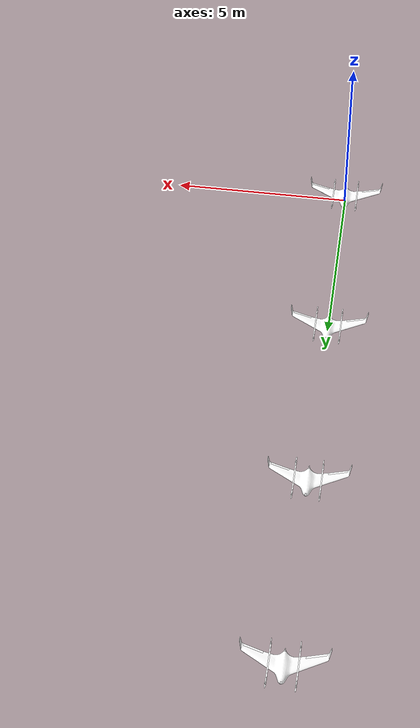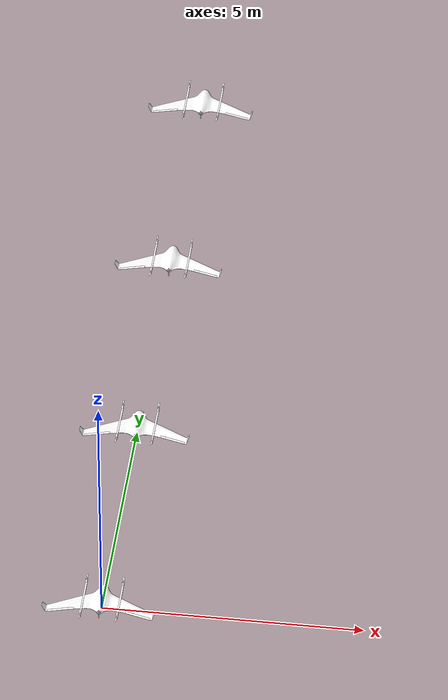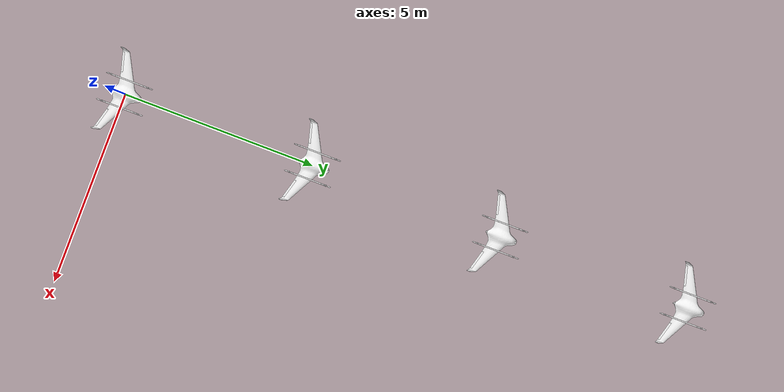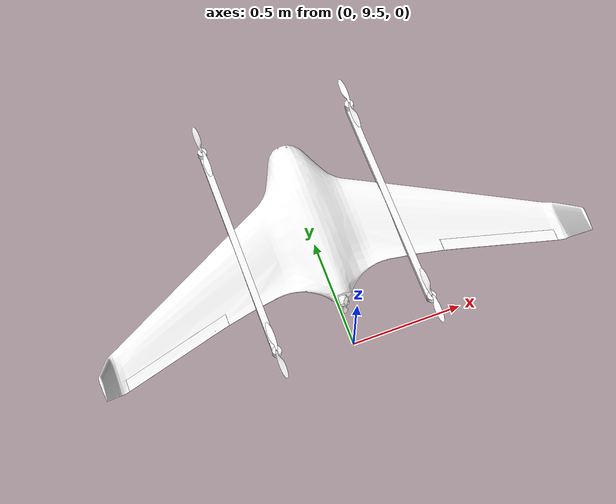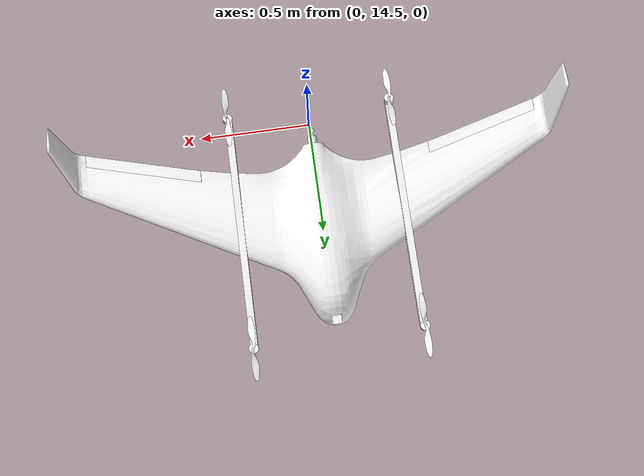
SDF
<sdf version="1.7">
 <world name="runway">
  <plugin filename="gz-sim-physics-system" name="gz::sim::systems::Physics"/>
  <plugin filename="gz-sim-user-commands-system" name="gz::sim::systems::UserCommands"/>
  <plugin filename="gz-sim-scene-broadcaster-system" name="gz::sim::systems::SceneBroadcaster"/>
  <plugin filename="gz-sim-imu-system" name="gz::sim::systems::Imu"/>
  <scene><ambient>1.0 1.0 1.0</ambient><background>0.8 0.8 0.8</background></scene>
  <light type="directional" name="sun">
   <pose>0 0 10 0 0 0</pose>
   <diffuse>0.8 0.8 0.8 1</diffuse>
   <specular>0.8 0.8 0.8 1</specular>
   <attenuation>
    <range>1000</range>
    <constant>0.9</constant>
    <linear>0.01</linear>
    <quadratic>0.001</quadratic>
   </attenuation>
   <direction>-0.5 0.1 -0.9</direction>
  </light>
  <include>
   <name>skywalker_x8_quad_0</name>
   <pose degrees="true">0 0 0.2 0 0 90</pose>
   <uri>model://skywalker_x8_quad_0</uri>
  </include>
  <include>
   <name>skywalker_x8_quad_1</name>
   <pose degrees="true">0 5 0.2 0 0 90</pose>
   <uri>model://skywalker_x8_quad_1</uri>
  </include>
  <include>
   <name>skywalker_x8_quad_2</name>
   <pose degrees="true">0 10 0.2 0 0 90</pose>
   <uri>model://skywalker_x8_quad_2</uri>
  </include>
  <include>
   <name>skywalker_x8_quad_3</name>
   <pose degrees="true">0 15 0.2 0 0 90</pose>
   <uri>model://skywalker_x8_quad_3</uri>
  </include>
 </world>
</sdf>

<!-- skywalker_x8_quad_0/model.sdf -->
<sdf version="1.7">
  <model name="skywalker_x8_quad_0">
    <pose>0 0 0.246 0 0 0</pose>

    <link name='base_link'>
      <pose>0 0 0 0 0 0</pose>
      <inertial>
        <pose>0 0 0 0 0 0</pose>
        <mass>4.5</mass>
        <inertia>
          <ixx>0.45</ixx>
          <ixy>0</ixy>
          <ixz>0.06</ixz>
          <iyy>0.325</iyy>
          <iyz>0</iyz>
          <izz>0.75</izz>
        </inertia>
      </inertial>
      <collision name='base_link_collision'>
        <pose>0 0 -0.07 0 0 0</pose>
        <geometry>
          <box>
            <size>0.80 2.15 0.2</size>
          </box>
        </geometry>
      </collision>
      <visual name='base_link_visual'>
        <geometry>
          <mesh>
            <uri>model://skywalker_x8/meshes/x8_wing.dae</uri>
          </mesh>
        </geometry>
        <material>
          <diffuse>1.0 1.0 1.0</diffuse>
          <specular>1.0 1.0 1.0</specular>
          <pbr>
            <metal>
                <albedo_map>model://skywalker_x8/materials/textures/x8.tga</albedo_map>
                <metalness>0.1</metalness>
            </metal>
          </pbr>
        </material>
      </visual>
      <visual name='left_motor_column'>
        <pose>0 0.35 0.01 0 0 0</pose>
        <geometry>
          <box>
            <size>0.98 0.03 0.03</size>
          </box>
        </geometry>
        <material>
          <ambient>1 1 1</ambient>
          <diffuse>1 1 1</diffuse>
          <specular>1 1 1</specular>
          <pbr>
            <metal>
              <albedo_map>model://skywalker_x8/materials/textures/metal_graphite/metal_graphite_basecolor.jpg</albedo_map>
              <metalness_map>model://skywalker_x8/materials/textures/metal_graphite/metal_graphite_metallic.jpg</metalness_map>
              <normal_map>model://skywalker_x8/materials/textures/metal_graphite/metal_graphite_normal.jpg</normal_map>
              <roughness_map>model://skywalker_x8/materials/textures/metal_graphite/metal_graphite_roughness.jpg</roughness_map>
              <roughness>1.0</roughness>
              <metalness>1.0</metalness>
            </metal>
          </pbr>
        </material>
      </visual>
      <visual name='right_motor_column'>
        <pose>0 -0.35 0.01 0 0 0</pose>
        <geometry>
          <box>
            <size>0.98 0.03 0.03</size>
          </box>
        </geometry>
        <material>
          <ambient>1 1 1</ambient>
          <diffuse>1 1 1</diffuse>
          <specular>1 1 1</specular>
          <pbr>
            <metal>
              <albedo_map>model://skywalker_x8/materials/textures/metal_graphite/metal_graphite_basecolor.jpg</albedo_map>
              <metalness_map>model://skywalker_x8/materials/textures/metal_graphite/metal_graphite_metallic.jpg</metalness_map>
              <normal_map>model://skywalker_x8/materials/textures/metal_graphite/metal_graphite_normal.jpg</normal_map>
              <roughness_map>model://skywalker_x8/materials/textures/metal_graphite/metal_graphite_roughness.jpg</roughness_map>
              <roughness>1.0</roughness>
              <metalness>1.0</metalness>
            </metal>
          </pbr>
        </material>
      </visual>
      <visual name='m0'>
        <pose degrees="true">0.49 -0.35 0.045 -3 0 0</pose>
        <geometry>
          <cylinder>
            <length>0.035</length>
            <radius>0.02</radius>
          </cylinder>
        </geometry>
        <material>
          <ambient>1 1 1</ambient>
          <diffuse>1 1 1</diffuse>
          <specular>1 1 1</specular>
          <pbr>
            <metal>
              <albedo_map>model://skywalker_x8/materials/textures/blue_metal/blue_metal_basecolor.jpg</albedo_map>
              <metalness_map>model://skywalker_x8/materials/textures/blue_metal/blue_metal_metallic.jpg</metalness_map>
              <normal_map>model://skywalker_x8/materials/textures/blue_metal/blue_metal_normal.jpg</normal_map>
              <roughness_map>model://skywalker_x8/materials/textures/blue_metal/blue_metal_roughness.jpg</roughness_map>
              <roughness>1.0</roughness>
              <metalness>1.0</metalness>
            </metal>
          </pbr>
        </material>
      </visual>
      <visual name='m1'>
        <pose degrees="true">-0.49 0.35 0.045 3 0 0</pose>
        <geometry>
          <cylinder>
            <length>0.035</length>
            <radius>0.02</radius>
          </cylinder>
        </geometry>
        <material>
          <ambient>1 1 1</ambient>
          <diffuse>1 1 1</diffuse>
          <specular>1 1 1</specular>
          <pbr>
            <metal>
              <albedo_map>model://skywalker_x8/materials/textures/blue_metal/blue_metal_basecolor.jpg</albedo_map>
              <metalness_map>model://skywalker_x8/materials/textures/blue_metal/blue_metal_metallic.jpg</metalness_map>
              <normal_map>model://skywalker_x8/materials/textures/blue_metal/blue_metal_normal.jpg</normal_map>
              <roughness_map>model://skywalker_x8/materials/textures/blue_metal/blue_metal_roughness.jpg</roughness_map>
              <roughness>1.0</roughness>
              <metalness>1.0</metalness>
            </metal>
          </pbr>
        </material>
      </visual>
      <visual name='m2'>
        <pose degrees="true">0.49 0.35 0.045 3 0 0</pose>
        <geometry>
          <cylinder>
            <length>0.035</length>
            <radius>0.02</radius>
          </cylinder>
        </geometry>
        <material>
          <ambient>1 1 1</ambient>
          <diffuse>1 1 1</diffuse>
          <specular>1 1 1</specular>
          <pbr>
            <metal>
              <albedo_map>model://skywalker_x8/materials/textures/blue_metal/blue_metal_basecolor.jpg</albedo_map>
              <metalness_map>model://skywalker_x8/materials/textures/blue_metal/blue_metal_metallic.jpg</metalness_map>
              <normal_map>model://skywalker_x8/materials/textures/blue_metal/blue_metal_normal.jpg</normal_map>
              <roughness_map>model://skywalker_x8/materials/textures/blue_metal/blue_metal_roughness.jpg</roughness_map>
              <roughness>1.0</roughness>
              <metalness>1.0</metalness>
            </metal>
          </pbr>
        </material>
      </visual>
      <visual name='m3'>
        <pose degrees="true">-0.49 -0.35 0.045 -3 0 0</pose>
        <geometry>
          <cylinder>
            <length>0.035</length>
            <radius>0.02</radius>
          </cylinder>
        </geometry>
        <material>
          <ambient>1 1 1</ambient>
          <diffuse>1 1 1</diffuse>
          <specular>1 1 1</specular>
          <pbr>
            <metal>
              <albedo_map>model://skywalker_x8/materials/textures/blue_metal/blue_metal_basecolor.jpg</albedo_map>
              <metalness_map>model://skywalker_x8/materials/textures/blue_metal/blue_metal_metallic.jpg</metalness_map>
              <normal_map>model://skywalker_x8/materials/textures/blue_metal/blue_metal_normal.jpg</normal_map>
              <roughness_map>model://skywalker_x8/materials/textures/blue_metal/blue_metal_roughness.jpg</roughness_map>
              <roughness>1.0</roughness>
              <metalness>1.0</metalness>
            </metal>
          </pbr>
        </material>
      </visual>
      <visual name='m4'>
        <pose degrees="true">-0.361 0 0.0 0 90 0</pose>
        <geometry>
          <cylinder>
            <length>0.035</length>
            <radius>0.02</radius>
          </cylinder>
        </geometry>
        <material>
          <ambient>1 1 1</ambient>
          <diffuse>1 1 1</diffuse>
          <specular>1 1 1</specular>
          <pbr>
            <metal>
              <albedo_map>model://skywalker_x8/materials/textures/blue_metal/blue_metal_basecolor.jpg</albedo_map>
              <metalness_map>model://skywalker_x8/materials/textures/blue_metal/blue_metal_metallic.jpg</metalness_map>
              <normal_map>model://skywalker_x8/materials/textures/blue_metal/blue_metal_normal.jpg</normal_map>
              <roughness_map>model://skywalker_x8/materials/textures/blue_metal/blue_metal_roughness.jpg</roughness_map>
              <roughness>1.0</roughness>
              <metalness>1.0</metalness>
            </metal>
          </pbr>
        </material>
      </visual>
      <!-- save for debugging use -->
    </link>

    <link name='rotor_0'>
      <pose degrees="true">0.49 -0.35 0.07 -3 0 0</pose>
      <inertial>
        <pose>0 0 0 0 0 0</pose>
        <mass>0.025</mass>
        <inertia>
          <ixx>9.75e-06</ixx>
          <ixy>0</ixy>
          <ixz>0</ixz>
          <iyy>0.000166704</iyy>
          <iyz>0</iyz>
          <izz>0.000167604</izz>
        </inertia>
      </inertial>
      <collision name='rotor_0_collision'>
        <pose>0 0 0 0 0 0</pose>
        <geometry>
          <cylinder>
            <length>0.005</length>
            <radius>0.105</radius>
          </cylinder>
        </geometry>
      </collision>
      <visual name='rotor_0_visual'>
        <pose>0 0 0 0 0 0</pose>
        <geometry>
          <mesh>
            <scale>1 1 1</scale>
            <uri>model://skywalker_x8/meshes/iris_prop_cw.dae</uri>
          </mesh>
        </geometry>
        <material>
          <diffuse>1.0 1.0 1.0</diffuse>
          <specular>1.0 1.0 1.0</specular>
          <pbr>
            <metal>
                <albedo_map>model://skywalker_x8/materials/textures/x8.tga</albedo_map>
                <metalness>0.5</metalness>
            </metal>
          </pbr>
        </material>
      </visual>
    </link>
    <joint name='rotor_0_joint' type='revolute'>
      <child>rotor_0</child>
      <parent>base_link</parent>
      <axis>
        <xyz>0 0 1</xyz>
        <limit>
          <lower>-1e+16</lower>
          <upper>1e+16</upper>
        </limit>
        <dynamics>
          <damping>0.002</damping>
        </dynamics>
        <use_parent_model_frame>1</use_parent_model_frame>
      </axis>
    </joint>

    <link name='rotor_1'>
      <pose degrees="true">-0.49 0.35 0.07 3 0 0</pose>
      <inertial>
        <pose>0 0 0 0 0 0</pose>
        <mass>0.025</mass>
        <inertia>
          <ixx>9.75e-06</ixx>
          <ixy>0</ixy>
          <ixz>0</ixz>
          <iyy>0.000166704</iyy>
          <iyz>0</iyz>
          <izz>0.000167604</izz>
        </inertia>
      </inertial>
      <collision name='rotor_1_collision'>
        <pose>0 0 0 0 0 0</pose>
        <geometry>
          <cylinder>
            <length>0.005</length>
            <radius>0.105</radius>
          </cylinder>
        </geometry>
      </collision>
      <visual name='rotor_1_visual'>
        <pose>0 0 0 0 0 0</pose>
        <geometry>
          <mesh>
            <scale>1 1 1</scale>
            <uri>model://skywalker_x8/meshes/iris_prop_cw.dae</uri>
          </mesh>
        </geometry>
        <material>
          <diffuse>1.0 1.0 1.0</diffuse>
          <specular>1.0 1.0 1.0</specular>
          <pbr>
            <metal>
                <albedo_map>model://skywalker_x8/materials/textures/x8.tga</albedo_map>
                <metalness>0.5</metalness>
            </metal>
          </pbr>
        </material>
      </visual>
    </link>
    <joint name='rotor_1_joint' type='revolute'>
      <child>rotor_1</child>
      <parent>base_link</parent>
      <axis>
        <xyz>0 0 1</xyz>
        <limit>
          <lower>-1e+16</lower>
          <upper>1e+16</upper>
        </limit>
        <dynamics>
          <damping>0.002</damping>
        </dynamics>
        <use_parent_model_frame>1</use_parent_model_frame>
      </axis>
    </joint>

    <link name='rotor_2'>
      <pose degrees="true">0.49 0.35 0.07 3 0 0</pose>
      <inertial>
        <pose>0 0 0 0 0 0</pose>
        <mass>0.025</mass>
        <inertia>
          <ixx>9.75e-06</ixx>
          <ixy>0</ixy>
          <ixz>0</ixz>
          <iyy>0.000166704</iyy>
          <iyz>0</iyz>
          <izz>0.000167604</izz>
        </inertia>
      </inertial>
      <collision name='rotor_2_collision'>
        <pose>0 0 0 0 0 0</pose>
        <geometry>
          <cylinder>
            <length>0.005</length>
            <radius>0.105</radius>
          </cylinder>
        </geometry>
      </collision>
      <visual name='rotor_2_visual'>
        <pose>0 0 0 0 0 0</pose>
        <geometry>
          <mesh>
            <scale>1 1 1</scale>
            <uri>model://skywalker_x8/meshes/iris_prop_ccw.dae</uri>
          </mesh>
        </geometry>
        <material>
          <diffuse>1.0 1.0 1.0</diffuse>
          <specular>1.0 1.0 1.0</specular>
          <pbr>
            <metal>
                <albedo_map>model://skywalker_x8/materials/textures/x8.tga</albedo_map>
                <metalness>0.5</metalness>
            </metal>
          </pbr>
        </material>
      </visual>
    </link>
    <joint name='rotor_2_joint' type='revolute'>
      <child>rotor_2</child>
      <parent>base_link</parent>
      <axis>
        <xyz>0 0 1</xyz>
        <limit>
          <lower>-1e+16</lower>
          <upper>1e+16</upper>
        </limit>
        <dynamics>
          <damping>0.002</damping>
        </dynamics>
        <use_parent_model_frame>1</use_parent_model_frame>
      </axis>
    </joint>

    <link name='rotor_3'>
      <pose degrees="true">-0.49 -0.35 0.07 -3 0 0</pose>
      <inertial>
        <pose>0 0 0 0 0 0</pose>
        <mass>0.025</mass>
        <inertia>
          <ixx>9.75e-06</ixx>
          <ixy>0</ixy>
          <ixz>0</ixz>
          <iyy>0.000166704</iyy>
          <iyz>0</iyz>
          <izz>0.000167604</izz>
        </inertia>
      </inertial>
      <collision name='rotor_3_collision'>
        <pose>0 0 0 0 0 0</pose>
        <geometry>
          <cylinder>
            <length>0.005</length>
            <radius>0.105</radius>
          </cylinder>
        </geometry>
      </collision>
      <visual name='rotor_3_visual'>
        <pose>0 0 0 0 0 0</pose>
        <geometry>
          <mesh>
            <scale>1 1 1</scale>
            <uri>model://skywalker_x8/meshes/iris_prop_ccw.dae</uri>
          </mesh>
        </geometry>
        <material>
          <diffuse>1.0 1.0 1.0</diffuse>
          <specular>1.0 1.0 1.0</specular>
          <pbr>
            <metal>
                <albedo_map>model://skywalker_x8/materials/textures/x8.tga</albedo_map>
                <metalness>0.5</metalness>
            </metal>
          </pbr>
        </material>
      </visual>
    </link>
    <joint name='rotor_3_joint' type='revolute'>
      <child>rotor_3</child>
      <parent>base_link</parent>
      <axis>
        <xyz>0 0 1</xyz>
        <limit>
          <lower>-1e+16</lower>
          <upper>1e+16</upper>
        </limit>
        <dynamics>
          <damping>0.002</damping>
        </dynamics>
        <use_parent_model_frame>1</use_parent_model_frame>
      </axis>
    </joint>

    <link name='rotor_pusher'>
      <pose degrees="true">-0.385 0 0.0 0 90 0</pose>
      <inertial>
        <mass>0.025</mass>
        <inertia>
          <ixx>9.75e-06</ixx>
          <ixy>0</ixy>
          <ixz>0</ixz>
          <iyy>0.000166704</iyy>
          <iyz>0</iyz>
          <izz>0.000167604</izz>
        </inertia>
      </inertial>
      <collision name='collision'>
        <pose>0 0 0 0 0 0</pose>
        <geometry>
          <cylinder>
            <length>0.005</length>
            <radius>0.065</radius>
          </cylinder>
        </geometry>
      </collision>
      <visual name='visual'>
        <pose>0 0 0 0 0 0</pose>
        <geometry>
          <mesh>
            <scale>0.8 0.8 0.8</scale>
            <uri>model://skywalker_x8/meshes/iris_prop_ccw.dae</uri>
          </mesh>
        </geometry>
        <material>
          <diffuse>1.0 1.0 1.0</diffuse>
          <specular>1.0 1.0 1.0</specular>
          <pbr>
            <metal>
                <albedo_map>model://skywalker_x8/materials/textures/x8.tga</albedo_map>
                <metalness>0.5</metalness>
            </metal>
          </pbr>
        </material>
      </visual>
    </link>
    <joint name='rotor_pusher_joint' type='revolute'>
      <child>rotor_pusher</child>
      <parent>base_link</parent>
      <axis>
        <xyz>0 0 1</xyz>
        <limit>
          <lower>-1e+16</lower>
          <upper>1e+16</upper>
        </limit>
        <dynamics>
          <damping>0.002</damping>
        </dynamics>
        <use_parent_model_frame>1</use_parent_model_frame>
      </axis>
    </joint>

    <link name="left_elevon">
      <inertial>
        <mass>0.1</mass>
        <inertia>
          <ixx>0.000102319</ixx>
          <ixy>0</ixy>
          <iyy>0.00334417</iyy>
          <ixz>0</ixz>
          <iyz>0</iyz>
          <izz>0.003446072</izz>
        </inertia>
        <pose>-0.30 0.75 -0.005 0 0 0</pose>
      </inertial>
      <visual name='left_elevon_visual'>
        <geometry>
          <mesh>
            <uri>model://skywalker_x8/meshes/x8_elevon_left.dae</uri>
          </mesh>
        </geometry>
        <material>
          <diffuse>1.0 1.0 1.0</diffuse>
          <specular>1.0 1.0 1.0</specular>
          <pbr>
            <metal>
                <albedo_map>model://skywalker_x8/materials/textures/x8.tga</albedo_map>
                <metalness>0.1</metalness>
            </metal>
          </pbr>
        </material>
      </visual>
    </link>

    <link name="right_elevon">
      <inertial>
        <mass>0.1</mass>
        <inertia>
          <ixx>0.000102319</ixx>
          <ixy>0</ixy>
          <iyy>0.00334417</iyy>
          <ixz>0</ixz>
          <iyz>0</iyz>
          <izz>0.003446072</izz>
        </inertia>
        <pose>-0.30 -0.75 -0.005 0 0 0</pose>
      </inertial>
      <visual name='right_elevon_visual'>
        <geometry>
          <mesh>
            <uri>model://skywalker_x8/meshes/x8_elevon_right.dae</uri>
          </mesh>
        </geometry>
        <material>
          <diffuse>1.0 1.0 1.0</diffuse>
          <specular>1.0 1.0 1.0</specular>
          <pbr>
            <metal>
                <albedo_map>model://skywalker_x8/materials/textures/x8.tga</albedo_map>
                <metalness>0.1</metalness>
            </metal>
          </pbr>
        </material>
      </visual>
    </link>

    <!-- Joint range -30/+30 deg. -->
    <joint name='left_elevon_joint' type='revolute'>
      <parent>base_link</parent>
      <child>left_elevon</child>
      <pose>-0.27 0.6 -0.005 0 0 0.265</pose>
      <axis>
        <xyz>0 1 0</xyz>
        <limit>
          <lower>-0.53</lower>
          <upper>0.53</upper>
        </limit>
        <dynamics>
          <damping>0.1</damping>
        </dynamics>
      </axis>
    </joint>

    <!-- Joint range -30/+30 deg. -->
    <joint name='right_elevon_joint' type='revolute'>
      <parent>base_link</parent>
      <child>right_elevon</child>
      <pose>-0.27 -0.6 -0.005 0 0 -0.265</pose>
      <axis>
        <xyz>0 1 0</xyz>
        <limit>
          <lower>-0.53</lower>
          <upper>0.53</upper>
        </limit>
        <dynamics>
          <damping>0.1</damping>
        </dynamics>
      </axis>
    </joint>

    <!-- sensors -->
    <link name='imu_link'>
      <inertial>
        <pose>0 0 0 0 0 0</pose>
        <mass>0.15</mass>
        <inertia>
          <ixx>0.00002</ixx>
          <ixy>0</ixy>
          <ixz>0</ixz>
          <iyy>0.00002</iyy>
          <iyz>0</iyz>
          <izz>0.00002</izz>
        </inertia>
      </inertial>
      <sensor name="imu_sensor" type="imu">
        <pose degrees="true">0 0 0 180 0 0</pose>
        <always_on>1</always_on>
        <update_rate>1000.0</update_rate>
      </sensor>
    </link>
    <joint name='skywalker_x8_quad/imu_joint' type='revolute'>
      <child>imu_link</child>
      <parent>base_link</parent>
      <axis>
        <xyz>0 0 1</xyz>
        <limit>
          <lower>0</lower>
          <upper>0</upper>
          <effort>0</effort>
          <velocity>0</velocity>
        </limit>
        <dynamics>
          <damping>1.0</damping>
        </dynamics>
        <use_parent_model_frame>1</use_parent_model_frame>
      </axis>
    </joint>

    <!-- plugins -->
    <plugin filename="gz-sim-joint-state-publisher-system"
      name="gz::sim::systems::JointStatePublisher">
    </plugin>
    <!-- rotor_0 lift-drag -->
    <plugin filename="gz-sim-lift-drag-system"
        name="gz::sim::systems::LiftDrag">
      <a0>0.3</a0>
      <alpha_stall>1.4</alpha_stall>
      <cla>4.2500</cla>
      <cda>0.10</cda>
      <cma>0.0</cma>
      <cla_stall>-0.025</cla_stall>
      <cda_stall>0.0</cda_stall>
      <cma_stall>0.0</cma_stall>
      <area>0.002</area>
      <air_density>1.2041</air_density>
      <cp>0.084 0 0</cp>
      <forward>0 -1 0</forward>
      <upward>0 0 1</upward>
      <link_name>rotor_0</link_name>
    </plugin>
    <plugin filename="gz-sim-lift-drag-system"
        name="gz::sim::systems::LiftDrag">
      <a0>0.3</a0>
      <alpha_stall>1.4</alpha_stall>
      <cla>4.2500</cla>
      <cda>0.10</cda>
      <cma>0.0</cma>
      <cla_stall>-0.025</cla_stall>
      <cda_stall>0.0</cda_stall>
      <cma_stall>0.0</cma_stall>
      <area>0.002</area>
      <air_density>1.2041</air_density>
      <cp>-0.084 0 0</cp>
      <forward>0 1 0</forward>
      <upward>0 0 1</upward>
      <link_name>rotor_0</link_name>
    </plugin>
    <!-- rotor_1 lift-drag -->
    <plugin filename="gz-sim-lift-drag-system"
        name="gz::sim::systems::LiftDrag">
      <a0>0.3</a0>
      <alpha_stall>1.4</alpha_stall>
      <cla>4.2500</cla>
      <cda>0.10</cda>
      <cma>0.0</cma>
      <cla_stall>-0.025</cla_stall>
      <cda_stall>0.0</cda_stall>
      <cma_stall>0.0</cma_stall>
      <area>0.002</area>
      <air_density>1.2041</air_density>
      <cp>0.084 0 0</cp>
      <forward>0 -1 0</forward>
      <upward>0 0 1</upward>
      <link_name>rotor_1</link_name>
    </plugin>
    <plugin filename="gz-sim-lift-drag-system"
        name="gz::sim::systems::LiftDrag">
      <a0>0.3</a0>
      <alpha_stall>1.4</alpha_stall>
      <cla>4.2500</cla>
      <cda>0.10</cda>
      <cma>0.0</cma>
      <cla_stall>-0.025</cla_stall>
      <cda_stall>0.0</cda_stall>
      <cma_stall>0.0</cma_stall>
      <area>0.002</area>
      <air_density>1.2041</air_density>
      <cp>-0.084 0 0</cp>
      <forward>0 1 0</forward>
      <upward>0 0 1</upward>
      <link_name>rotor_1</link_name>
    </plugin>
    <!-- rotor_2 lift-drag -->
    <plugin filename="gz-sim-lift-drag-system"
        name="gz::sim::systems::LiftDrag">
      <a0>0.3</a0>
      <alpha_stall>1.4</alpha_stall>
      <cla>4.2500</cla>
      <cda>0.10</cda>
      <cma>0.0</cma>
      <cla_stall>-0.025</cla_stall>
      <cda_stall>0.0</cda_stall>
      <cma_stall>0.0</cma_stall>
      <area>0.002</area>
      <air_density>1.2041</air_density>
      <cp>0.084 0 0</cp>
      <forward>0 1 0</forward>
      <upward>0 0 1</upward>
      <link_name>rotor_2</link_name>
    </plugin>
    <plugin filename="gz-sim-lift-drag-system"
        name="gz::sim::systems::LiftDrag">
      <a0>0.3</a0>
      <alpha_stall>1.4</alpha_stall>
      <cla>4.2500</cla>
      <cda>0.10</cda>
      <cma>0.0</cma>
      <cla_stall>-0.025</cla_stall>
      <cda_stall>0.0</cda_stall>
      <cma_stall>0.0</cma_stall>
      <area>0.002</area>
      <air_density>1.2041</air_density>
      <cp>-0.084 0 0</cp>
      <forward>0 -1 0</forward>
      <upward>0 0 1</upward>
      <link_name>rotor_2</link_name>
    </plugin>
    <!-- rotor_3 lift-drag -->
    <plugin filename="gz-sim-lift-drag-system"
        name="gz::sim::systems::LiftDrag">
      <a0>0.3</a0>
      <alpha_stall>1.4</alpha_stall>
      <cla>4.2500</cla>
      <cda>0.10</cda>
      <cma>0.0</cma>
      <cla_stall>-0.025</cla_stall>
      <cda_stall>0.0</cda_stall>
      <cma_stall>0.0</cma_stall>
      <area>0.002</area>
      <air_density>1.2041</air_density>
      <cp>0.084 0 0</cp>
      <forward>0 1 0</forward>
      <upward>0 0 1</upward>
      <link_name>rotor_3</link_name>
    </plugin>
    <plugin filename="gz-sim-lift-drag-system"
        name="gz::sim::systems::LiftDrag">
      <a0>0.3</a0>
      <alpha_stall>1.4</alpha_stall>
      <cla>4.2500</cla>
      <cda>0.10</cda>
      <cma>0.0</cma>
      <cla_stall>-0.025</cla_stall>
      <cda_stall>0.0</cda_stall>
      <cma_stall>0.0</cma_stall>
      <area>0.002</area>
      <air_density>1.2041</air_density>
      <cp>-0.084 0 0</cp>
      <forward>0 -1 0</forward>
      <upward>0 0 1</upward>
      <link_name>rotor_3</link_name>
    </plugin>
    <!-- rotor_pusher lift-drag -->
    <plugin filename="gz-sim-lift-drag-system"
        name="gz::sim::systems::LiftDrag">
      <a0>0.30</a0>
      <alpha_stall>1.4</alpha_stall>
      <cla>4.2500</cla>
      <cda>0.10</cda>
      <cma>0.0</cma>
      <cla_stall>-0.025</cla_stall>
      <cda_stall>0.0</cda_stall>
      <cma_stall>0.0</cma_stall>
      <area>0.02</area>
      <air_density>1.2041</air_density>
      <cp>0.074205 0 0</cp>
      <forward>0 1 0</forward>
      <upward>0 0 1</upward>
      <link_name>rotor_pusher</link_name>
    </plugin>
    <plugin filename="gz-sim-lift-drag-system"
        name="gz::sim::systems::LiftDrag">
      <a0>0.30</a0>
      <alpha_stall>1.4</alpha_stall>
      <cla>4.2500</cla>
      <cda>0.10</cda>
      <cma>0.0</cma>
      <cla_stall>-0.025</cla_stall>
      <cda_stall>0.0</cda_stall>
      <cma_stall>0.0</cma_stall>
      <area>0.02</area>
      <air_density>1.2041</air_density>
      <cp>-0.074205 0 0</cp>
      <forward>0 -1 0</forward>
      <upward>0 0 1</upward>
      <link_name>rotor_pusher</link_name>
    </plugin>
    <!-- wing lift-drag -->
    <plugin filename="gz-sim-lift-drag-system"
        name="gz::sim::systems::LiftDrag">
      <a0>0.13</a0>
      <cla>3.7</cla>
      <cda>0.06417112299</cda>
      <cma>0.0</cma>
      <alpha_stall>0.3391428111</alpha_stall>
      <cla_stall>-3.85</cla_stall>
      <cda_stall>-0.9233984055</cda_stall>
      <cma_stall>0.0</cma_stall>
      <cp>0.01 0 0</cp>
      <area>0.80</area>
      <air_density>1.2041</air_density>
      <forward>1 0 0</forward>
      <upward>0 0 1</upward>
      <link_name>base_link</link_name>
    </plugin>
    <!-- left_elevon lift-drag -->
    <plugin filename="gz-sim-lift-drag-system"
        name="gz::sim::systems::LiftDrag">
      <a0>0.15</a0>
      <cla>6.8</cla>
      <cda>0.06417112299</cda>
      <cma>0.0</cma>
      <alpha_stall>0.6391428111</alpha_stall>
      <cla_stall>-3.85</cla_stall>
      <cda_stall>-0.9233984055</cda_stall>
      <cma_stall>0.0</cma_stall>
      <cp>-0.30 0.75 -0.005</cp>
      <area>0.10</area>
      <air_density>1.2041</air_density>
      <forward>1 0 0</forward>
      <upward>0 0 1</upward>
      <link_name>base_link</link_name>
      <control_joint_name>left_elevon_joint</control_joint_name>
      <control_joint_rad_to_cl>-5.0</control_joint_rad_to_cl>
    </plugin>
    <!-- right_elevon lift-drag -->
    <plugin filename="gz-sim-lift-drag-system"
        name="gz::sim::systems::LiftDrag">
      <a0>0.15</a0>
      <cla>6.8</cla>
      <cda>0.06417112299</cda>
      <cma>0.0</cma>
      <alpha_stall>0.6391428111</alpha_stall>
      <cla_stall>-3.85</cla_stall>
      <cda_stall>-0.9233984055</cda_stall>
      <cma_stall>0.0</cma_stall>
      <cp>-0.30 -0.75 -0.005</cp>
      <area>0.10</area>
      <air_density>1.2041</air_density>
      <forward>1 0 0</forward>
      <upward>0 0 1</upward>
      <link_name>base_link</link_name>
      <control_joint_name>right_elevon_joint</control_joint_name>
      <control_joint_rad_to_cl>-5.0</control_joint_rad_to_cl>
    </plugin>
    <!-- left_winglet lift-drag -->
    <plugin filename="gz-sim-lift-drag-system"
        name="gz::sim::systems::LiftDrag">
      <a0>0.0</a0>
      <cla>4.752798721</cla>
      <cda>0.6417112299</cda>
      <cma>0.0</cma>
      <alpha_stall>0.3391428111</alpha_stall>
      <cla_stall>-3.85</cla_stall>
      <cda_stall>-0.9233984055</cda_stall>
      <cma_stall>0.0</cma_stall>
      <cp>-0.36 1.04 0.08</cp>
      <area>0.12</area>
      <air_density>1.2041</air_density>
      <forward>1 0 0</forward>
      <upward>0 1 0</upward>
      <link_name>base_link</link_name>
    </plugin>
    <!-- right_winglet lift-drag -->
    <plugin filename="gz-sim-lift-drag-system"
        name="gz::sim::systems::LiftDrag">
      <a0>0.0</a0>
      <cla>4.752798721</cla>
      <cda>0.6417112299</cda>
      <cma>0.0</cma>
      <alpha_stall>0.3391428111</alpha_stall>
      <cla_stall>-3.85</cla_stall>
      <cda_stall>-0.9233984055</cda_stall>
      <cma_stall>0.0</cma_stall>
      <cp>-0.36 -1.04 0.08</cp>
      <area>0.12</area>
      <air_density>1.2041</air_density>
      <forward>1 0 0</forward>
      <upward>0 -1 0</upward>
      <link_name>base_link</link_name>
    </plugin>

    <plugin filename="gz-sim-apply-joint-force-system"
      name="gz::sim::systems::ApplyJointForce">
      <joint_name>rotor_0_joint</joint_name>
    </plugin>
    <plugin filename="gz-sim-apply-joint-force-system"
      name="gz::sim::systems::ApplyJointForce">
      <joint_name>rotor_1_joint</joint_name>
    </plugin>
    <plugin filename="gz-sim-apply-joint-force-system"
      name="gz::sim::systems::ApplyJointForce">
      <joint_name>rotor_2_joint</joint_name>
    </plugin>
    <plugin filename="gz-sim-apply-joint-force-system"
      name="gz::sim::systems::ApplyJointForce">
      <joint_name>rotor_3_joint</joint_name>
    </plugin>
    <plugin filename="gz-sim-apply-joint-force-system"
      name="gz::sim::systems::ApplyJointForce">
      <joint_name>rotor_pusher_joint</joint_name>
    </plugin>
    <plugin filename="gz-sim-apply-joint-force-system"
      name="gz::sim::systems::ApplyJointForce">
      <joint_name>left_elevon_joint</joint_name>
    </plugin>
    <plugin filename="gz-sim-apply-joint-force-system"
      name="gz::sim::systems::ApplyJointForce">
      <joint_name>right_elevon_joint</joint_name>
    </plugin>

    <plugin name="ArduPilotPlugin" filename="ArduPilotPlugin">
      <!-- Port settings -->
      <fdm_addr>127.0.0.1</fdm_addr>
      <fdm_port_in>9002</fdm_port_in>
      <connectionTimeoutMaxCount>5</connectionTimeoutMaxCount>
      <lock_step>1</lock_step>

      <modelXYZToAirplaneXForwardZDown degrees="true">0 0 0 180 0 0</modelXYZToAirplaneXForwardZDown>
      <gazeboXYZToNED degrees="true">0 0 0 180 0 90</gazeboXYZToNED>

      <!-- Sensors -->
      <imuName>imu_sensor</imuName>

      <!--
          incoming control command [0, 1]
          so offset it by 0 to get [0, 1]
          and divide max target by 1.
          offset = 0
          multiplier = 838 max rpm / 1 = 838
        -->

      <!--
          SERVO3_FUNCTION   70 (Throttle)
          SERVO3_MAX        2000
          SERVO3_MIN        1000
          SERVO3_REVERSED   0
          SERVO3_TRIM       1000
       -->
      <control channel="2">
        <jointName>rotor_pusher_joint</jointName>
        <useForce>1</useForce>
        <multiplier>838</multiplier>
        <offset>0</offset>
        <servo_min>1000</servo_min>
        <servo_max>2000</servo_max>
        <type>VELOCITY</type>
        <p_gain>0.20</p_gain>
        <i_gain>0</i_gain>
        <d_gain>0</d_gain>
        <i_max>0</i_max>
        <i_min>0</i_min>
        <cmd_max>2.5</cmd_max>
        <cmd_min>-2.5</cmd_min>
      </control>

      <control channel="0">
        <jointName>left_elevon_joint</jointName>
        <useForce>1</useForce>
        <multiplier>1.048</multiplier>
        <offset>-0.5</offset>
        <servo_min>1100</servo_min>
        <servo_max>1900</servo_max>
        <type>POSITION</type>
        <p_gain>10.0</p_gain>
        <i_gain>0</i_gain>
        <d_gain>0</d_gain>
        <i_max>0</i_max>
        <i_min>0</i_min>
        <cmd_max>2.5</cmd_max>
        <cmd_min>-2.5</cmd_min>
      </control>

      <!--
          SERVO2_FUNCTION   78 (Elevon Right)
          SERVO2_MAX        1900
          SERVO2_MIN        1100
          SERVO2_REVERSED   0
          SERVO2_TRIM       1500
       -->
      <control channel="1">
        <jointName>right_elevon_joint</jointName>
        <useForce>1</useForce>
        <multiplier>1.048</multiplier>
        <offset>-0.5</offset>
        <servo_min>1100</servo_min>
        <servo_max>1900</servo_max>
        <type>POSITION</type>
        <p_gain>10.0</p_gain>
        <i_gain>0</i_gain>
        <d_gain>0</d_gain>
        <i_max>0</i_max>
        <i_min>0</i_min>
        <cmd_max>2.5</cmd_max>
        <cmd_min>-2.5</cmd_min>
      </control>

      <!--
          SERVO5_FUNCTION   33 (Motor1 Front Right CCW)
          SERVO5_MAX        1900
          SERVO5_MIN        1100
          SERVO5_REVERSED   0
          SERVO5_TRIM       1500
       -->
      <control channel="4">
        <jointName>rotor_0_joint</jointName>
        <useForce>1</useForce>
        <multiplier>-1500</multiplier>
        <offset>0</offset>
        <servo_min>1100</servo_min>
        <servo_max>1900</servo_max>
        <type>VELOCITY</type>
        <p_gain>0.20</p_gain>
        <i_gain>0</i_gain>
        <d_gain>0</d_gain>
        <i_max>0</i_max>
        <i_min>0</i_min>
        <cmd_max>2.5</cmd_max>
        <cmd_min>-2.5</cmd_min>
      </control>

      <!--
          SERVO6_FUNCTION   34 (Motor2 Rear Left CCW)
          SERVO6_MAX        1900
          SERVO6_MIN        1100
          SERVO6_REVERSED   0
          SERVO6_TRIM       1500
       -->
      <control channel="5">
        <jointName>rotor_1_joint</jointName>
        <useForce>1</useForce>
        <multiplier>-1500</multiplier>
        <offset>0</offset>
        <servo_min>1100</servo_min>
        <servo_max>1900</servo_max>
        <type>VELOCITY</type>
        <p_gain>0.20</p_gain>
        <i_gain>0</i_gain>
        <d_gain>0</d_gain>
        <i_max>0</i_max>
        <i_min>0</i_min>
        <cmd_max>2.5</cmd_max>
        <cmd_min>-2.5</cmd_min>
      </control>

      <!--
          SERVO7_FUNCTION   35 (Motor3 Front Left CW)
          SERVO7_MAX        1900
          SERVO7_MIN        1100
          SERVO7_REVERSED   0
          SERVO7_TRIM       1500
       -->
      <control channel="6">
        <jointName>rotor_2_joint</jointName>
        <useForce>1</useForce>
        <multiplier>1500</multiplier>
        <offset>0</offset>
        <servo_min>1100</servo_min>
        <servo_max>1900</servo_max>
        <type>VELOCITY</type>
        <p_gain>0.20</p_gain>
        <i_gain>0</i_gain>
        <d_gain>0</d_gain>
        <i_max>0</i_max>
        <i_min>0</i_min>
        <cmd_max>2.5</cmd_max>
        <cmd_min>-2.5</cmd_min>
      </control>

      <!--
          SERVO8_FUNCTION   36 (Motor4 Rear Right CW)
          SERVO8_MAX        1900
          SERVO8_MIN        1100
          SERVO8_REVERSED   0
          SERVO8_TRIM       1500
       -->
      <control channel="7">
        <jointName>rotor_3_joint</jointName>
        <useForce>1</useForce>
        <multiplier>1500</multiplier>
        <offset>0</offset>
        <servo_min>1100</servo_min>
        <servo_max>1900</servo_max>
        <type>VELOCITY</type>
        <p_gain>0.20</p_gain>
        <i_gain>0</i_gain>
        <d_gain>0</d_gain>
        <i_max>0</i_max>
        <i_min>0</i_min>
        <cmd_max>2.5</cmd_max>
        <cmd_min>-2.5</cmd_min>
      </control>

    </plugin>
  </model>
</sdf>

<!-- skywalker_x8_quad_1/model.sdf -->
<sdf version="1.7">
  <model name="skywalker_x8_quad_1">
    <pose>0 0 0.246 0 0 0</pose>

    <link name='base_link'>
      <pose>0 0 0 0 0 0</pose>
      <inertial>
        <pose>0 0 0 0 0 0</pose>
        <mass>4.5</mass>
        <inertia>
          <ixx>0.45</ixx>
          <ixy>0</ixy>
          <ixz>0.06</ixz>
          <iyy>0.325</iyy>
          <iyz>0</iyz>
          <izz>0.75</izz>
        </inertia>
      </inertial>
      <collision name='base_link_collision'>
        <pose>0 0 -0.07 0 0 0</pose>
        <geometry>
          <box>
            <size>0.80 2.15 0.2</size>
          </box>
        </geometry>
      </collision>
      <visual name='base_link_visual'>
        <geometry>
          <mesh>
            <uri>model://skywalker_x8/meshes/x8_wing.dae</uri>
          </mesh>
        </geometry>
        <material>
          <diffuse>1.0 1.0 1.0</diffuse>
          <specular>1.0 1.0 1.0</specular>
          <pbr>
            <metal>
                <albedo_map>model://skywalker_x8/materials/textures/x8.tga</albedo_map>
                <metalness>0.1</metalness>
            </metal>
          </pbr>
        </material>
      </visual>
      <visual name='left_motor_column'>
        <pose>0 0.35 0.01 0 0 0</pose>
        <geometry>
          <box>
            <size>0.98 0.03 0.03</size>
          </box>
        </geometry>
        <material>
          <ambient>1 1 1</ambient>
          <diffuse>1 1 1</diffuse>
          <specular>1 1 1</specular>
          <pbr>
            <metal>
              <albedo_map>model://skywalker_x8/materials/textures/metal_graphite/metal_graphite_basecolor.jpg</albedo_map>
              <metalness_map>model://skywalker_x8/materials/textures/metal_graphite/metal_graphite_metallic.jpg</metalness_map>
              <normal_map>model://skywalker_x8/materials/textures/metal_graphite/metal_graphite_normal.jpg</normal_map>
              <roughness_map>model://skywalker_x8/materials/textures/metal_graphite/metal_graphite_roughness.jpg</roughness_map>
              <roughness>1.0</roughness>
              <metalness>1.0</metalness>
            </metal>
          </pbr>
        </material>
      </visual>
      <visual name='right_motor_column'>
        <pose>0 -0.35 0.01 0 0 0</pose>
        <geometry>
          <box>
            <size>0.98 0.03 0.03</size>
          </box>
        </geometry>
        <material>
          <ambient>1 1 1</ambient>
          <diffuse>1 1 1</diffuse>
          <specular>1 1 1</specular>
          <pbr>
            <metal>
              <albedo_map>model://skywalker_x8/materials/textures/metal_graphite/metal_graphite_basecolor.jpg</albedo_map>
              <metalness_map>model://skywalker_x8/materials/textures/metal_graphite/metal_graphite_metallic.jpg</metalness_map>
              <normal_map>model://skywalker_x8/materials/textures/metal_graphite/metal_graphite_normal.jpg</normal_map>
              <roughness_map>model://skywalker_x8/materials/textures/metal_graphite/metal_graphite_roughness.jpg</roughness_map>
              <roughness>1.0</roughness>
              <metalness>1.0</metalness>
            </metal>
          </pbr>
        </material>
      </visual>
      <visual name='m0'>
        <pose degrees="true">0.49 -0.35 0.045 -3 0 0</pose>
        <geometry>
          <cylinder>
            <length>0.035</length>
            <radius>0.02</radius>
          </cylinder>
        </geometry>
        <material>
          <ambient>1 1 1</ambient>
          <diffuse>1 1 1</diffuse>
          <specular>1 1 1</specular>
          <pbr>
            <metal>
              <albedo_map>model://skywalker_x8/materials/textures/blue_metal/blue_metal_basecolor.jpg</albedo_map>
              <metalness_map>model://skywalker_x8/materials/textures/blue_metal/blue_metal_metallic.jpg</metalness_map>
              <normal_map>model://skywalker_x8/materials/textures/blue_metal/blue_metal_normal.jpg</normal_map>
              <roughness_map>model://skywalker_x8/materials/textures/blue_metal/blue_metal_roughness.jpg</roughness_map>
              <roughness>1.0</roughness>
              <metalness>1.0</metalness>
            </metal>
          </pbr>
        </material>
      </visual>
      <visual name='m1'>
        <pose degrees="true">-0.49 0.35 0.045 3 0 0</pose>
        <geometry>
          <cylinder>
            <length>0.035</length>
            <radius>0.02</radius>
          </cylinder>
        </geometry>
        <material>
          <ambient>1 1 1</ambient>
          <diffuse>1 1 1</diffuse>
          <specular>1 1 1</specular>
          <pbr>
            <metal>
              <albedo_map>model://skywalker_x8/materials/textures/blue_metal/blue_metal_basecolor.jpg</albedo_map>
              <metalness_map>model://skywalker_x8/materials/textures/blue_metal/blue_metal_metallic.jpg</metalness_map>
              <normal_map>model://skywalker_x8/materials/textures/blue_metal/blue_metal_normal.jpg</normal_map>
              <roughness_map>model://skywalker_x8/materials/textures/blue_metal/blue_metal_roughness.jpg</roughness_map>
              <roughness>1.0</roughness>
              <metalness>1.0</metalness>
            </metal>
          </pbr>
        </material>
      </visual>
      <visual name='m2'>
        <pose degrees="true">0.49 0.35 0.045 3 0 0</pose>
        <geometry>
          <cylinder>
            <length>0.035</length>
            <radius>0.02</radius>
          </cylinder>
        </geometry>
        <material>
          <ambient>1 1 1</ambient>
          <diffuse>1 1 1</diffuse>
          <specular>1 1 1</specular>
          <pbr>
            <metal>
              <albedo_map>model://skywalker_x8/materials/textures/blue_metal/blue_metal_basecolor.jpg</albedo_map>
              <metalness_map>model://skywalker_x8/materials/textures/blue_metal/blue_metal_metallic.jpg</metalness_map>
              <normal_map>model://skywalker_x8/materials/textures/blue_metal/blue_metal_normal.jpg</normal_map>
              <roughness_map>model://skywalker_x8/materials/textures/blue_metal/blue_metal_roughness.jpg</roughness_map>
              <roughness>1.0</roughness>
              <metalness>1.0</metalness>
            </metal>
          </pbr>
        </material>
      </visual>
      <visual name='m3'>
        <pose degrees="true">-0.49 -0.35 0.045 -3 0 0</pose>
        <geometry>
          <cylinder>
            <length>0.035</length>
            <radius>0.02</radius>
          </cylinder>
        </geometry>
        <material>
          <ambient>1 1 1</ambient>
          <diffuse>1 1 1</diffuse>
          <specular>1 1 1</specular>
          <pbr>
            <metal>
              <albedo_map>model://skywalker_x8/materials/textures/blue_metal/blue_metal_basecolor.jpg</albedo_map>
              <metalness_map>model://skywalker_x8/materials/textures/blue_metal/blue_metal_metallic.jpg</metalness_map>
              <normal_map>model://skywalker_x8/materials/textures/blue_metal/blue_metal_normal.jpg</normal_map>
              <roughness_map>model://skywalker_x8/materials/textures/blue_metal/blue_metal_roughness.jpg</roughness_map>
              <roughness>1.0</roughness>
              <metalness>1.0</metalness>
            </metal>
          </pbr>
        </material>
      </visual>
      <visual name='m4'>
        <pose degrees="true">-0.361 0 0.0 0 90 0</pose>
        <geometry>
          <cylinder>
            <length>0.035</length>
            <radius>0.02</radius>
          </cylinder>
        </geometry>
        <material>
          <ambient>1 1 1</ambient>
          <diffuse>1 1 1</diffuse>
          <specular>1 1 1</specular>
          <pbr>
            <metal>
              <albedo_map>model://skywalker_x8/materials/textures/blue_metal/blue_metal_basecolor.jpg</albedo_map>
              <metalness_map>model://skywalker_x8/materials/textures/blue_metal/blue_metal_metallic.jpg</metalness_map>
              <normal_map>model://skywalker_x8/materials/textures/blue_metal/blue_metal_normal.jpg</normal_map>
              <roughness_map>model://skywalker_x8/materials/textures/blue_metal/blue_metal_roughness.jpg</roughness_map>
              <roughness>1.0</roughness>
              <metalness>1.0</metalness>
            </metal>
          </pbr>
        </material>
      </visual>
      <!-- save for debugging use -->
    </link>

    <link name='rotor_0'>
      <pose degrees="true">0.49 -0.35 0.07 -3 0 0</pose>
      <inertial>
        <pose>0 0 0 0 0 0</pose>
        <mass>0.025</mass>
        <inertia>
          <ixx>9.75e-06</ixx>
          <ixy>0</ixy>
          <ixz>0</ixz>
          <iyy>0.000166704</iyy>
          <iyz>0</iyz>
          <izz>0.000167604</izz>
        </inertia>
      </inertial>
      <collision name='rotor_0_collision'>
        <pose>0 0 0 0 0 0</pose>
        <geometry>
          <cylinder>
            <length>0.005</length>
            <radius>0.105</radius>
          </cylinder>
        </geometry>
      </collision>
      <visual name='rotor_0_visual'>
        <pose>0 0 0 0 0 0</pose>
        <geometry>
          <mesh>
            <scale>1 1 1</scale>
            <uri>model://skywalker_x8/meshes/iris_prop_cw.dae</uri>
          </mesh>
        </geometry>
        <material>
          <diffuse>1.0 1.0 1.0</diffuse>
          <specular>1.0 1.0 1.0</specular>
          <pbr>
            <metal>
                <albedo_map>model://skywalker_x8/materials/textures/x8.tga</albedo_map>
                <metalness>0.5</metalness>
            </metal>
          </pbr>
        </material>
      </visual>
    </link>
    <joint name='rotor_0_joint' type='revolute'>
      <child>rotor_0</child>
      <parent>base_link</parent>
      <axis>
        <xyz>0 0 1</xyz>
        <limit>
          <lower>-1e+16</lower>
          <upper>1e+16</upper>
        </limit>
        <dynamics>
          <damping>0.002</damping>
        </dynamics>
        <use_parent_model_frame>1</use_parent_model_frame>
      </axis>
    </joint>

    <link name='rotor_1'>
      <pose degrees="true">-0.49 0.35 0.07 3 0 0</pose>
      <inertial>
        <pose>0 0 0 0 0 0</pose>
        <mass>0.025</mass>
        <inertia>
          <ixx>9.75e-06</ixx>
          <ixy>0</ixy>
          <ixz>0</ixz>
          <iyy>0.000166704</iyy>
          <iyz>0</iyz>
          <izz>0.000167604</izz>
        </inertia>
      </inertial>
      <collision name='rotor_1_collision'>
        <pose>0 0 0 0 0 0</pose>
        <geometry>
          <cylinder>
            <length>0.005</length>
            <radius>0.105</radius>
          </cylinder>
        </geometry>
      </collision>
      <visual name='rotor_1_visual'>
        <pose>0 0 0 0 0 0</pose>
        <geometry>
          <mesh>
            <scale>1 1 1</scale>
            <uri>model://skywalker_x8/meshes/iris_prop_cw.dae</uri>
          </mesh>
        </geometry>
        <material>
          <diffuse>1.0 1.0 1.0</diffuse>
          <specular>1.0 1.0 1.0</specular>
          <pbr>
            <metal>
                <albedo_map>model://skywalker_x8/materials/textures/x8.tga</albedo_map>
                <metalness>0.5</metalness>
            </metal>
          </pbr>
        </material>
      </visual>
    </link>
    <joint name='rotor_1_joint' type='revolute'>
      <child>rotor_1</child>
      <parent>base_link</parent>
      <axis>
        <xyz>0 0 1</xyz>
        <limit>
          <lower>-1e+16</lower>
          <upper>1e+16</upper>
        </limit>
        <dynamics>
          <damping>0.002</damping>
        </dynamics>
        <use_parent_model_frame>1</use_parent_model_frame>
      </axis>
    </joint>

    <link name='rotor_2'>
      <pose degrees="true">0.49 0.35 0.07 3 0 0</pose>
      <inertial>
        <pose>0 0 0 0 0 0</pose>
        <mass>0.025</mass>
        <inertia>
          <ixx>9.75e-06</ixx>
          <ixy>0</ixy>
          <ixz>0</ixz>
          <iyy>0.000166704</iyy>
          <iyz>0</iyz>
          <izz>0.000167604</izz>
        </inertia>
      </inertial>
      <collision name='rotor_2_collision'>
        <pose>0 0 0 0 0 0</pose>
        <geometry>
          <cylinder>
            <length>0.005</length>
            <radius>0.105</radius>
          </cylinder>
        </geometry>
      </collision>
      <visual name='rotor_2_visual'>
        <pose>0 0 0 0 0 0</pose>
        <geometry>
          <mesh>
            <scale>1 1 1</scale>
            <uri>model://skywalker_x8/meshes/iris_prop_ccw.dae</uri>
          </mesh>
        </geometry>
        <material>
          <diffuse>1.0 1.0 1.0</diffuse>
          <specular>1.0 1.0 1.0</specular>
          <pbr>
            <metal>
                <albedo_map>model://skywalker_x8/materials/textures/x8.tga</albedo_map>
                <metalness>0.5</metalness>
            </metal>
          </pbr>
        </material>
      </visual>
    </link>
    <joint name='rotor_2_joint' type='revolute'>
      <child>rotor_2</child>
      <parent>base_link</parent>
      <axis>
        <xyz>0 0 1</xyz>
        <limit>
          <lower>-1e+16</lower>
          <upper>1e+16</upper>
        </limit>
        <dynamics>
          <damping>0.002</damping>
        </dynamics>
        <use_parent_model_frame>1</use_parent_model_frame>
      </axis>
    </joint>

    <link name='rotor_3'>
      <pose degrees="true">-0.49 -0.35 0.07 -3 0 0</pose>
      <inertial>
        <pose>0 0 0 0 0 0</pose>
        <mass>0.025</mass>
        <inertia>
          <ixx>9.75e-06</ixx>
          <ixy>0</ixy>
          <ixz>0</ixz>
          <iyy>0.000166704</iyy>
          <iyz>0</iyz>
          <izz>0.000167604</izz>
        </inertia>
      </inertial>
      <collision name='rotor_3_collision'>
        <pose>0 0 0 0 0 0</pose>
        <geometry>
          <cylinder>
            <length>0.005</length>
            <radius>0.105</radius>
          </cylinder>
        </geometry>
      </collision>
      <visual name='rotor_3_visual'>
        <pose>0 0 0 0 0 0</pose>
        <geometry>
          <mesh>
            <scale>1 1 1</scale>
            <uri>model://skywalker_x8/meshes/iris_prop_ccw.dae</uri>
          </mesh>
        </geometry>
        <material>
          <diffuse>1.0 1.0 1.0</diffuse>
          <specular>1.0 1.0 1.0</specular>
          <pbr>
            <metal>
                <albedo_map>model://skywalker_x8/materials/textures/x8.tga</albedo_map>
                <metalness>0.5</metalness>
            </metal>
          </pbr>
        </material>
      </visual>
    </link>
    <joint name='rotor_3_joint' type='revolute'>
      <child>rotor_3</child>
      <parent>base_link</parent>
      <axis>
        <xyz>0 0 1</xyz>
        <limit>
          <lower>-1e+16</lower>
          <upper>1e+16</upper>
        </limit>
        <dynamics>
          <damping>0.002</damping>
        </dynamics>
        <use_parent_model_frame>1</use_parent_model_frame>
      </axis>
    </joint>

    <link name='rotor_pusher'>
      <pose degrees="true">-0.385 0 0.0 0 90 0</pose>
      <inertial>
        <mass>0.025</mass>
        <inertia>
          <ixx>9.75e-06</ixx>
          <ixy>0</ixy>
          <ixz>0</ixz>
          <iyy>0.000166704</iyy>
          <iyz>0</iyz>
          <izz>0.000167604</izz>
        </inertia>
      </inertial>
      <collision name='collision'>
        <pose>0 0 0 0 0 0</pose>
        <geometry>
          <cylinder>
            <length>0.005</length>
            <radius>0.065</radius>
          </cylinder>
        </geometry>
      </collision>
      <visual name='visual'>
        <pose>0 0 0 0 0 0</pose>
        <geometry>
          <mesh>
            <scale>0.8 0.8 0.8</scale>
            <uri>model://skywalker_x8/meshes/iris_prop_ccw.dae</uri>
          </mesh>
        </geometry>
        <material>
          <diffuse>1.0 1.0 1.0</diffuse>
          <specular>1.0 1.0 1.0</specular>
          <pbr>
            <metal>
                <albedo_map>model://skywalker_x8/materials/textures/x8.tga</albedo_map>
                <metalness>0.5</metalness>
            </metal>
          </pbr>
        </material>
      </visual>
    </link>
    <joint name='rotor_pusher_joint' type='revolute'>
      <child>rotor_pusher</child>
      <parent>base_link</parent>
      <axis>
        <xyz>0 0 1</xyz>
        <limit>
          <lower>-1e+16</lower>
          <upper>1e+16</upper>
        </limit>
        <dynamics>
          <damping>0.002</damping>
        </dynamics>
        <use_parent_model_frame>1</use_parent_model_frame>
      </axis>
    </joint>

    <link name="left_elevon">
      <inertial>
        <mass>0.1</mass>
        <inertia>
          <ixx>0.000102319</ixx>
          <ixy>0</ixy>
          <iyy>0.00334417</iyy>
          <ixz>0</ixz>
          <iyz>0</iyz>
          <izz>0.003446072</izz>
        </inertia>
        <pose>-0.30 0.75 -0.005 0 0 0</pose>
      </inertial>
      <visual name='left_elevon_visual'>
        <geometry>
          <mesh>
            <uri>model://skywalker_x8/meshes/x8_elevon_left.dae</uri>
          </mesh>
        </geometry>
        <material>
          <diffuse>1.0 1.0 1.0</diffuse>
          <specular>1.0 1.0 1.0</specular>
          <pbr>
            <metal>
                <albedo_map>model://skywalker_x8/materials/textures/x8.tga</albedo_map>
                <metalness>0.1</metalness>
            </metal>
          </pbr>
        </material>
      </visual>
    </link>

    <link name="right_elevon">
      <inertial>
        <mass>0.1</mass>
        <inertia>
          <ixx>0.000102319</ixx>
          <ixy>0</ixy>
          <iyy>0.00334417</iyy>
          <ixz>0</ixz>
          <iyz>0</iyz>
          <izz>0.003446072</izz>
        </inertia>
        <pose>-0.30 -0.75 -0.005 0 0 0</pose>
      </inertial>
      <visual name='right_elevon_visual'>
        <geometry>
          <mesh>
            <uri>model://skywalker_x8/meshes/x8_elevon_right.dae</uri>
          </mesh>
        </geometry>
        <material>
          <diffuse>1.0 1.0 1.0</diffuse>
          <specular>1.0 1.0 1.0</specular>
          <pbr>
            <metal>
                <albedo_map>model://skywalker_x8/materials/textures/x8.tga</albedo_map>
                <metalness>0.1</metalness>
            </metal>
          </pbr>
        </material>
      </visual>
    </link>

    <!-- Joint range -30/+30 deg. -->
    <joint name='left_elevon_joint' type='revolute'>
      <parent>base_link</parent>
      <child>left_elevon</child>
      <pose>-0.27 0.6 -0.005 0 0 0.265</pose>
      <axis>
        <xyz>0 1 0</xyz>
        <limit>
          <lower>-0.53</lower>
          <upper>0.53</upper>
        </limit>
        <dynamics>
          <damping>0.1</damping>
        </dynamics>
      </axis>
    </joint>

    <!-- Joint range -30/+30 deg. -->
    <joint name='right_elevon_joint' type='revolute'>
      <parent>base_link</parent>
      <child>right_elevon</child>
      <pose>-0.27 -0.6 -0.005 0 0 -0.265</pose>
      <axis>
        <xyz>0 1 0</xyz>
        <limit>
          <lower>-0.53</lower>
          <upper>0.53</upper>
        </limit>
        <dynamics>
          <damping>0.1</damping>
        </dynamics>
      </axis>
    </joint>

    <!-- sensors -->
    <link name='imu_link'>
      <inertial>
        <pose>0 0 0 0 0 0</pose>
        <mass>0.15</mass>
        <inertia>
          <ixx>0.00002</ixx>
          <ixy>0</ixy>
          <ixz>0</ixz>
          <iyy>0.00002</iyy>
          <iyz>0</iyz>
          <izz>0.00002</izz>
        </inertia>
      </inertial>
      <sensor name="imu_sensor" type="imu">
        <pose degrees="true">0 0 0 180 0 0</pose>
        <always_on>1</always_on>
        <update_rate>1000.0</update_rate>
      </sensor>
    </link>
    <joint name='skywalker_x8_quad/imu_joint' type='revolute'>
      <child>imu_link</child>
      <parent>base_link</parent>
      <axis>
        <xyz>0 0 1</xyz>
        <limit>
          <lower>0</lower>
          <upper>0</upper>
          <effort>0</effort>
          <velocity>0</velocity>
        </limit>
        <dynamics>
          <damping>1.0</damping>
        </dynamics>
        <use_parent_model_frame>1</use_parent_model_frame>
      </axis>
    </joint>

    <!-- plugins -->
    <plugin filename="gz-sim-joint-state-publisher-system"
      name="gz::sim::systems::JointStatePublisher">
    </plugin>
    <!-- rotor_0 lift-drag -->
    <plugin filename="gz-sim-lift-drag-system"
        name="gz::sim::systems::LiftDrag">
      <a0>0.3</a0>
      <alpha_stall>1.4</alpha_stall>
      <cla>4.2500</cla>
      <cda>0.10</cda>
      <cma>0.0</cma>
      <cla_stall>-0.025</cla_stall>
      <cda_stall>0.0</cda_stall>
      <cma_stall>0.0</cma_stall>
      <area>0.002</area>
      <air_density>1.2041</air_density>
      <cp>0.084 0 0</cp>
      <forward>0 -1 0</forward>
      <upward>0 0 1</upward>
      <link_name>rotor_0</link_name>
    </plugin>
    <plugin filename="gz-sim-lift-drag-system"
        name="gz::sim::systems::LiftDrag">
      <a0>0.3</a0>
      <alpha_stall>1.4</alpha_stall>
      <cla>4.2500</cla>
      <cda>0.10</cda>
      <cma>0.0</cma>
      <cla_stall>-0.025</cla_stall>
      <cda_stall>0.0</cda_stall>
      <cma_stall>0.0</cma_stall>
      <area>0.002</area>
      <air_density>1.2041</air_density>
      <cp>-0.084 0 0</cp>
      <forward>0 1 0</forward>
      <upward>0 0 1</upward>
      <link_name>rotor_0</link_name>
    </plugin>
    <!-- rotor_1 lift-drag -->
    <plugin filename="gz-sim-lift-drag-system"
        name="gz::sim::systems::LiftDrag">
      <a0>0.3</a0>
      <alpha_stall>1.4</alpha_stall>
      <cla>4.2500</cla>
      <cda>0.10</cda>
      <cma>0.0</cma>
      <cla_stall>-0.025</cla_stall>
      <cda_stall>0.0</cda_stall>
      <cma_stall>0.0</cma_stall>
      <area>0.002</area>
      <air_density>1.2041</air_density>
      <cp>0.084 0 0</cp>
      <forward>0 -1 0</forward>
      <upward>0 0 1</upward>
      <link_name>rotor_1</link_name>
    </plugin>
    <plugin filename="gz-sim-lift-drag-system"
        name="gz::sim::systems::LiftDrag">
      <a0>0.3</a0>
      <alpha_stall>1.4</alpha_stall>
      <cla>4.2500</cla>
      <cda>0.10</cda>
      <cma>0.0</cma>
      <cla_stall>-0.025</cla_stall>
      <cda_stall>0.0</cda_stall>
      <cma_stall>0.0</cma_stall>
      <area>0.002</area>
      <air_density>1.2041</air_density>
      <cp>-0.084 0 0</cp>
      <forward>0 1 0</forward>
      <upward>0 0 1</upward>
      <link_name>rotor_1</link_name>
    </plugin>
    <!-- rotor_2 lift-drag -->
    <plugin filename="gz-sim-lift-drag-system"
        name="gz::sim::systems::LiftDrag">
      <a0>0.3</a0>
      <alpha_stall>1.4</alpha_stall>
      <cla>4.2500</cla>
      <cda>0.10</cda>
      <cma>0.0</cma>
      <cla_stall>-0.025</cla_stall>
      <cda_stall>0.0</cda_stall>
      <cma_stall>0.0</cma_stall>
      <area>0.002</area>
      <air_density>1.2041</air_density>
      <cp>0.084 0 0</cp>
      <forward>0 1 0</forward>
      <upward>0 0 1</upward>
      <link_name>rotor_2</link_name>
    </plugin>
    <plugin filename="gz-sim-lift-drag-system"
        name="gz::sim::systems::LiftDrag">
      <a0>0.3</a0>
      <alpha_stall>1.4</alpha_stall>
      <cla>4.2500</cla>
      <cda>0.10</cda>
      <cma>0.0</cma>
      <cla_stall>-0.025</cla_stall>
      <cda_stall>0.0</cda_stall>
      <cma_stall>0.0</cma_stall>
      <area>0.002</area>
      <air_density>1.2041</air_density>
      <cp>-0.084 0 0</cp>
      <forward>0 -1 0</forward>
      <upward>0 0 1</upward>
      <link_name>rotor_2</link_name>
    </plugin>
    <!-- rotor_3 lift-drag -->
    <plugin filename="gz-sim-lift-drag-system"
        name="gz::sim::systems::LiftDrag">
      <a0>0.3</a0>
      <alpha_stall>1.4</alpha_stall>
      <cla>4.2500</cla>
      <cda>0.10</cda>
      <cma>0.0</cma>
      <cla_stall>-0.025</cla_stall>
      <cda_stall>0.0</cda_stall>
      <cma_stall>0.0</cma_stall>
      <area>0.002</area>
      <air_density>1.2041</air_density>
      <cp>0.084 0 0</cp>
      <forward>0 1 0</forward>
      <upward>0 0 1</upward>
      <link_name>rotor_3</link_name>
    </plugin>
    <plugin filename="gz-sim-lift-drag-system"
        name="gz::sim::systems::LiftDrag">
      <a0>0.3</a0>
      <alpha_stall>1.4</alpha_stall>
      <cla>4.2500</cla>
      <cda>0.10</cda>
      <cma>0.0</cma>
      <cla_stall>-0.025</cla_stall>
      <cda_stall>0.0</cda_stall>
      <cma_stall>0.0</cma_stall>
      <area>0.002</area>
      <air_density>1.2041</air_density>
      <cp>-0.084 0 0</cp>
      <forward>0 -1 0</forward>
      <upward>0 0 1</upward>
      <link_name>rotor_3</link_name>
    </plugin>
    <!-- rotor_pusher lift-drag -->
    <plugin filename="gz-sim-lift-drag-system"
        name="gz::sim::systems::LiftDrag">
      <a0>0.30</a0>
      <alpha_stall>1.4</alpha_stall>
      <cla>4.2500</cla>
      <cda>0.10</cda>
      <cma>0.0</cma>
      <cla_stall>-0.025</cla_stall>
      <cda_stall>0.0</cda_stall>
      <cma_stall>0.0</cma_stall>
      <area>0.02</area>
      <air_density>1.2041</air_density>
      <cp>0.074205 0 0</cp>
      <forward>0 1 0</forward>
      <upward>0 0 1</upward>
      <link_name>rotor_pusher</link_name>
    </plugin>
    <plugin filename="gz-sim-lift-drag-system"
        name="gz::sim::systems::LiftDrag">
      <a0>0.30</a0>
      <alpha_stall>1.4</alpha_stall>
      <cla>4.2500</cla>
      <cda>0.10</cda>
      <cma>0.0</cma>
      <cla_stall>-0.025</cla_stall>
      <cda_stall>0.0</cda_stall>
      <cma_stall>0.0</cma_stall>
      <area>0.02</area>
      <air_density>1.2041</air_density>
      <cp>-0.074205 0 0</cp>
      <forward>0 -1 0</forward>
      <upward>0 0 1</upward>
      <link_name>rotor_pusher</link_name>
    </plugin>
    <!-- wing lift-drag -->
    <plugin filename="gz-sim-lift-drag-system"
        name="gz::sim::systems::LiftDrag">
      <a0>0.13</a0>
      <cla>3.7</cla>
      <cda>0.06417112299</cda>
      <cma>0.0</cma>
      <alpha_stall>0.3391428111</alpha_stall>
      <cla_stall>-3.85</cla_stall>
      <cda_stall>-0.9233984055</cda_stall>
      <cma_stall>0.0</cma_stall>
      <cp>0.01 0 0</cp>
      <area>0.80</area>
      <air_density>1.2041</air_density>
      <forward>1 0 0</forward>
      <upward>0 0 1</upward>
      <link_name>base_link</link_name>
    </plugin>
    <!-- left_elevon lift-drag -->
    <plugin filename="gz-sim-lift-drag-system"
        name="gz::sim::systems::LiftDrag">
      <a0>0.15</a0>
      <cla>6.8</cla>
      <cda>0.06417112299</cda>
      <cma>0.0</cma>
      <alpha_stall>0.6391428111</alpha_stall>
      <cla_stall>-3.85</cla_stall>
      <cda_stall>-0.9233984055</cda_stall>
      <cma_stall>0.0</cma_stall>
      <cp>-0.30 0.75 -0.005</cp>
      <area>0.10</area>
      <air_density>1.2041</air_density>
      <forward>1 0 0</forward>
      <upward>0 0 1</upward>
      <link_name>base_link</link_name>
      <control_joint_name>left_elevon_joint</control_joint_name>
      <control_joint_rad_to_cl>-5.0</control_joint_rad_to_cl>
    </plugin>
    <!-- right_elevon lift-drag -->
    <plugin filename="gz-sim-lift-drag-system"
        name="gz::sim::systems::LiftDrag">
      <a0>0.15</a0>
      <cla>6.8</cla>
      <cda>0.06417112299</cda>
      <cma>0.0</cma>
      <alpha_stall>0.6391428111</alpha_stall>
      <cla_stall>-3.85</cla_stall>
      <cda_stall>-0.9233984055</cda_stall>
      <cma_stall>0.0</cma_stall>
      <cp>-0.30 -0.75 -0.005</cp>
      <area>0.10</area>
      <air_density>1.2041</air_density>
      <forward>1 0 0</forward>
      <upward>0 0 1</upward>
      <link_name>base_link</link_name>
      <control_joint_name>right_elevon_joint</control_joint_name>
      <control_joint_rad_to_cl>-5.0</control_joint_rad_to_cl>
    </plugin>
    <!-- left_winglet lift-drag -->
    <plugin filename="gz-sim-lift-drag-system"
        name="gz::sim::systems::LiftDrag">
      <a0>0.0</a0>
      <cla>4.752798721</cla>
      <cda>0.6417112299</cda>
      <cma>0.0</cma>
      <alpha_stall>0.3391428111</alpha_stall>
      <cla_stall>-3.85</cla_stall>
      <cda_stall>-0.9233984055</cda_stall>
      <cma_stall>0.0</cma_stall>
      <cp>-0.36 1.04 0.08</cp>
      <area>0.12</area>
      <air_density>1.2041</air_density>
      <forward>1 0 0</forward>
      <upward>0 1 0</upward>
      <link_name>base_link</link_name>
    </plugin>
    <!-- right_winglet lift-drag -->
    <plugin filename="gz-sim-lift-drag-system"
        name="gz::sim::systems::LiftDrag">
      <a0>0.0</a0>
      <cla>4.752798721</cla>
      <cda>0.6417112299</cda>
      <cma>0.0</cma>
      <alpha_stall>0.3391428111</alpha_stall>
      <cla_stall>-3.85</cla_stall>
      <cda_stall>-0.9233984055</cda_stall>
      <cma_stall>0.0</cma_stall>
      <cp>-0.36 -1.04 0.08</cp>
      <area>0.12</area>
      <air_density>1.2041</air_density>
      <forward>1 0 0</forward>
      <upward>0 -1 0</upward>
      <link_name>base_link</link_name>
    </plugin>

    <plugin filename="gz-sim-apply-joint-force-system"
      name="gz::sim::systems::ApplyJointForce">
      <joint_name>rotor_0_joint</joint_name>
    </plugin>
    <plugin filename="gz-sim-apply-joint-force-system"
      name="gz::sim::systems::ApplyJointForce">
      <joint_name>rotor_1_joint</joint_name>
    </plugin>
    <plugin filename="gz-sim-apply-joint-force-system"
      name="gz::sim::systems::ApplyJointForce">
      <joint_name>rotor_2_joint</joint_name>
    </plugin>
    <plugin filename="gz-sim-apply-joint-force-system"
      name="gz::sim::systems::ApplyJointForce">
      <joint_name>rotor_3_joint</joint_name>
    </plugin>
    <plugin filename="gz-sim-apply-joint-force-system"
      name="gz::sim::systems::ApplyJointForce">
      <joint_name>rotor_pusher_joint</joint_name>
    </plugin>
    <plugin filename="gz-sim-apply-joint-force-system"
      name="gz::sim::systems::ApplyJointForce">
      <joint_name>left_elevon_joint</joint_name>
    </plugin>
    <plugin filename="gz-sim-apply-joint-force-system"
      name="gz::sim::systems::ApplyJointForce">
      <joint_name>right_elevon_joint</joint_name>
    </plugin>

    <plugin name="ArduPilotPlugin" filename="ArduPilotPlugin">
      <!-- Port settings -->
      <fdm_addr>127.0.0.1</fdm_addr>
      <fdm_port_in>9012</fdm_port_in>
      <connectionTimeoutMaxCount>5</connectionTimeoutMaxCount>
      <lock_step>1</lock_step>

      <modelXYZToAirplaneXForwardZDown degrees="true">0 0 0 180 0 0</modelXYZToAirplaneXForwardZDown>
      <gazeboXYZToNED degrees="true">0 0 0 180 0 90</gazeboXYZToNED>

      <!-- Sensors -->
      <imuName>imu_sensor</imuName>

      <!--
          incoming control command [0, 1]
          so offset it by 0 to get [0, 1]
          and divide max target by 1.
          offset = 0
          multiplier = 838 max rpm / 1 = 838
        -->

      <!--
          SERVO3_FUNCTION   70 (Throttle)
          SERVO3_MAX        2000
          SERVO3_MIN        1000
          SERVO3_REVERSED   0
          SERVO3_TRIM       1000
       -->
      <control channel="2">
        <jointName>rotor_pusher_joint</jointName>
        <useForce>1</useForce>
        <multiplier>838</multiplier>
        <offset>0</offset>
        <servo_min>1000</servo_min>
        <servo_max>2000</servo_max>
        <type>VELOCITY</type>
        <p_gain>0.20</p_gain>
        <i_gain>0</i_gain>
        <d_gain>0</d_gain>
        <i_max>0</i_max>
        <i_min>0</i_min>
        <cmd_max>2.5</cmd_max>
        <cmd_min>-2.5</cmd_min>
      </control>

      <control channel="0">
        <jointName>left_elevon_joint</jointName>
        <useForce>1</useForce>
        <multiplier>1.048</multiplier>
        <offset>-0.5</offset>
        <servo_min>1100</servo_min>
        <servo_max>1900</servo_max>
        <type>POSITION</type>
        <p_gain>10.0</p_gain>
        <i_gain>0</i_gain>
        <d_gain>0</d_gain>
        <i_max>0</i_max>
        <i_min>0</i_min>
        <cmd_max>2.5</cmd_max>
        <cmd_min>-2.5</cmd_min>
      </control>

      <!--
          SERVO2_FUNCTION   78 (Elevon Right)
          SERVO2_MAX        1900
          SERVO2_MIN        1100
          SERVO2_REVERSED   0
          SERVO2_TRIM       1500
       -->
      <control channel="1">
        <jointName>right_elevon_joint</jointName>
        <useForce>1</useForce>
        <multiplier>1.048</multiplier>
        <offset>-0.5</offset>
        <servo_min>1100</servo_min>
        <servo_max>1900</servo_max>
        <type>POSITION</type>
        <p_gain>10.0</p_gain>
        <i_gain>0</i_gain>
        <d_gain>0</d_gain>
        <i_max>0</i_max>
        <i_min>0</i_min>
        <cmd_max>2.5</cmd_max>
        <cmd_min>-2.5</cmd_min>
      </control>

      <!--
          SERVO5_FUNCTION   33 (Motor1 Front Right CCW)
          SERVO5_MAX        1900
          SERVO5_MIN        1100
          SERVO5_REVERSED   0
          SERVO5_TRIM       1500
       -->
      <control channel="4">
        <jointName>rotor_0_joint</jointName>
        <useForce>1</useForce>
        <multiplier>-1500</multiplier>
        <offset>0</offset>
        <servo_min>1100</servo_min>
        <servo_max>1900</servo_max>
        <type>VELOCITY</type>
        <p_gain>0.20</p_gain>
        <i_gain>0</i_gain>
        <d_gain>0</d_gain>
        <i_max>0</i_max>
        <i_min>0</i_min>
        <cmd_max>2.5</cmd_max>
        <cmd_min>-2.5</cmd_min>
      </control>

      <!--
          SERVO6_FUNCTION   34 (Motor2 Rear Left CCW)
          SERVO6_MAX        1900
          SERVO6_MIN        1100
          SERVO6_REVERSED   0
          SERVO6_TRIM       1500
       -->
      <control channel="5">
        <jointName>rotor_1_joint</jointName>
        <useForce>1</useForce>
        <multiplier>-1500</multiplier>
        <offset>0</offset>
        <servo_min>1100</servo_min>
        <servo_max>1900</servo_max>
        <type>VELOCITY</type>
        <p_gain>0.20</p_gain>
        <i_gain>0</i_gain>
        <d_gain>0</d_gain>
        <i_max>0</i_max>
        <i_min>0</i_min>
        <cmd_max>2.5</cmd_max>
        <cmd_min>-2.5</cmd_min>
      </control>

      <!--
          SERVO7_FUNCTION   35 (Motor3 Front Left CW)
          SERVO7_MAX        1900
          SERVO7_MIN        1100
          SERVO7_REVERSED   0
          SERVO7_TRIM       1500
       -->
      <control channel="6">
        <jointName>rotor_2_joint</jointName>
        <useForce>1</useForce>
        <multiplier>1500</multiplier>
        <offset>0</offset>
        <servo_min>1100</servo_min>
        <servo_max>1900</servo_max>
        <type>VELOCITY</type>
        <p_gain>0.20</p_gain>
        <i_gain>0</i_gain>
        <d_gain>0</d_gain>
        <i_max>0</i_max>
        <i_min>0</i_min>
        <cmd_max>2.5</cmd_max>
        <cmd_min>-2.5</cmd_min>
      </control>

      <!--
          SERVO8_FUNCTION   36 (Motor4 Rear Right CW)
          SERVO8_MAX        1900
          SERVO8_MIN        1100
          SERVO8_REVERSED   0
          SERVO8_TRIM       1500
       -->
      <control channel="7">
        <jointName>rotor_3_joint</jointName>
        <useForce>1</useForce>
        <multiplier>1500</multiplier>
        <offset>0</offset>
        <servo_min>1100</servo_min>
        <servo_max>1900</servo_max>
        <type>VELOCITY</type>
        <p_gain>0.20</p_gain>
        <i_gain>0</i_gain>
        <d_gain>0</d_gain>
        <i_max>0</i_max>
        <i_min>0</i_min>
        <cmd_max>2.5</cmd_max>
        <cmd_min>-2.5</cmd_min>
      </control>

    </plugin>
  </model>
</sdf>

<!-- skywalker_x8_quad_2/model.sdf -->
<sdf version="1.7">
  <model name="skywalker_x8_quad_2">
    <pose>0 0 0.246 0 0 0</pose>

    <link name='base_link'>
      <pose>0 0 0 0 0 0</pose>
      <inertial>
        <pose>0 0 0 0 0 0</pose>
        <mass>4.5</mass>
        <inertia>
          <ixx>0.45</ixx>
          <ixy>0</ixy>
          <ixz>0.06</ixz>
          <iyy>0.325</iyy>
          <iyz>0</iyz>
          <izz>0.75</izz>
        </inertia>
      </inertial>
      <collision name='base_link_collision'>
        <pose>0 0 -0.07 0 0 0</pose>
        <geometry>
          <box>
            <size>0.80 2.15 0.2</size>
          </box>
        </geometry>
      </collision>
      <visual name='base_link_visual'>
        <geometry>
          <mesh>
            <uri>model://skywalker_x8/meshes/x8_wing.dae</uri>
          </mesh>
        </geometry>
        <material>
          <diffuse>1.0 1.0 1.0</diffuse>
          <specular>1.0 1.0 1.0</specular>
          <pbr>
            <metal>
                <albedo_map>model://skywalker_x8/materials/textures/x8.tga</albedo_map>
                <metalness>0.1</metalness>
            </metal>
          </pbr>
        </material>
      </visual>
      <visual name='left_motor_column'>
        <pose>0 0.35 0.01 0 0 0</pose>
        <geometry>
          <box>
            <size>0.98 0.03 0.03</size>
          </box>
        </geometry>
        <material>
          <ambient>1 1 1</ambient>
          <diffuse>1 1 1</diffuse>
          <specular>1 1 1</specular>
          <pbr>
            <metal>
              <albedo_map>model://skywalker_x8/materials/textures/metal_graphite/metal_graphite_basecolor.jpg</albedo_map>
              <metalness_map>model://skywalker_x8/materials/textures/metal_graphite/metal_graphite_metallic.jpg</metalness_map>
              <normal_map>model://skywalker_x8/materials/textures/metal_graphite/metal_graphite_normal.jpg</normal_map>
              <roughness_map>model://skywalker_x8/materials/textures/metal_graphite/metal_graphite_roughness.jpg</roughness_map>
              <roughness>1.0</roughness>
              <metalness>1.0</metalness>
            </metal>
          </pbr>
        </material>
      </visual>
      <visual name='right_motor_column'>
        <pose>0 -0.35 0.01 0 0 0</pose>
        <geometry>
          <box>
            <size>0.98 0.03 0.03</size>
          </box>
        </geometry>
        <material>
          <ambient>1 1 1</ambient>
          <diffuse>1 1 1</diffuse>
          <specular>1 1 1</specular>
          <pbr>
            <metal>
              <albedo_map>model://skywalker_x8/materials/textures/metal_graphite/metal_graphite_basecolor.jpg</albedo_map>
              <metalness_map>model://skywalker_x8/materials/textures/metal_graphite/metal_graphite_metallic.jpg</metalness_map>
              <normal_map>model://skywalker_x8/materials/textures/metal_graphite/metal_graphite_normal.jpg</normal_map>
              <roughness_map>model://skywalker_x8/materials/textures/metal_graphite/metal_graphite_roughness.jpg</roughness_map>
              <roughness>1.0</roughness>
              <metalness>1.0</metalness>
            </metal>
          </pbr>
        </material>
      </visual>
      <visual name='m0'>
        <pose degrees="true">0.49 -0.35 0.045 -3 0 0</pose>
        <geometry>
          <cylinder>
            <length>0.035</length>
            <radius>0.02</radius>
          </cylinder>
        </geometry>
        <material>
          <ambient>1 1 1</ambient>
          <diffuse>1 1 1</diffuse>
          <specular>1 1 1</specular>
          <pbr>
            <metal>
              <albedo_map>model://skywalker_x8/materials/textures/blue_metal/blue_metal_basecolor.jpg</albedo_map>
              <metalness_map>model://skywalker_x8/materials/textures/blue_metal/blue_metal_metallic.jpg</metalness_map>
              <normal_map>model://skywalker_x8/materials/textures/blue_metal/blue_metal_normal.jpg</normal_map>
              <roughness_map>model://skywalker_x8/materials/textures/blue_metal/blue_metal_roughness.jpg</roughness_map>
              <roughness>1.0</roughness>
              <metalness>1.0</metalness>
            </metal>
          </pbr>
        </material>
      </visual>
      <visual name='m1'>
        <pose degrees="true">-0.49 0.35 0.045 3 0 0</pose>
        <geometry>
          <cylinder>
            <length>0.035</length>
            <radius>0.02</radius>
          </cylinder>
        </geometry>
        <material>
          <ambient>1 1 1</ambient>
          <diffuse>1 1 1</diffuse>
          <specular>1 1 1</specular>
          <pbr>
            <metal>
              <albedo_map>model://skywalker_x8/materials/textures/blue_metal/blue_metal_basecolor.jpg</albedo_map>
              <metalness_map>model://skywalker_x8/materials/textures/blue_metal/blue_metal_metallic.jpg</metalness_map>
              <normal_map>model://skywalker_x8/materials/textures/blue_metal/blue_metal_normal.jpg</normal_map>
              <roughness_map>model://skywalker_x8/materials/textures/blue_metal/blue_metal_roughness.jpg</roughness_map>
              <roughness>1.0</roughness>
              <metalness>1.0</metalness>
            </metal>
          </pbr>
        </material>
      </visual>
      <visual name='m2'>
        <pose degrees="true">0.49 0.35 0.045 3 0 0</pose>
        <geometry>
          <cylinder>
            <length>0.035</length>
            <radius>0.02</radius>
          </cylinder>
        </geometry>
        <material>
          <ambient>1 1 1</ambient>
          <diffuse>1 1 1</diffuse>
          <specular>1 1 1</specular>
          <pbr>
            <metal>
              <albedo_map>model://skywalker_x8/materials/textures/blue_metal/blue_metal_basecolor.jpg</albedo_map>
              <metalness_map>model://skywalker_x8/materials/textures/blue_metal/blue_metal_metallic.jpg</metalness_map>
              <normal_map>model://skywalker_x8/materials/textures/blue_metal/blue_metal_normal.jpg</normal_map>
              <roughness_map>model://skywalker_x8/materials/textures/blue_metal/blue_metal_roughness.jpg</roughness_map>
              <roughness>1.0</roughness>
              <metalness>1.0</metalness>
            </metal>
          </pbr>
        </material>
      </visual>
      <visual name='m3'>
        <pose degrees="true">-0.49 -0.35 0.045 -3 0 0</pose>
        <geometry>
          <cylinder>
            <length>0.035</length>
            <radius>0.02</radius>
          </cylinder>
        </geometry>
        <material>
          <ambient>1 1 1</ambient>
          <diffuse>1 1 1</diffuse>
          <specular>1 1 1</specular>
          <pbr>
            <metal>
              <albedo_map>model://skywalker_x8/materials/textures/blue_metal/blue_metal_basecolor.jpg</albedo_map>
              <metalness_map>model://skywalker_x8/materials/textures/blue_metal/blue_metal_metallic.jpg</metalness_map>
              <normal_map>model://skywalker_x8/materials/textures/blue_metal/blue_metal_normal.jpg</normal_map>
              <roughness_map>model://skywalker_x8/materials/textures/blue_metal/blue_metal_roughness.jpg</roughness_map>
              <roughness>1.0</roughness>
              <metalness>1.0</metalness>
            </metal>
          </pbr>
        </material>
      </visual>
      <visual name='m4'>
        <pose degrees="true">-0.361 0 0.0 0 90 0</pose>
        <geometry>
          <cylinder>
            <length>0.035</length>
            <radius>0.02</radius>
          </cylinder>
        </geometry>
        <material>
          <ambient>1 1 1</ambient>
          <diffuse>1 1 1</diffuse>
          <specular>1 1 1</specular>
          <pbr>
            <metal>
              <albedo_map>model://skywalker_x8/materials/textures/blue_metal/blue_metal_basecolor.jpg</albedo_map>
              <metalness_map>model://skywalker_x8/materials/textures/blue_metal/blue_metal_metallic.jpg</metalness_map>
              <normal_map>model://skywalker_x8/materials/textures/blue_metal/blue_metal_normal.jpg</normal_map>
              <roughness_map>model://skywalker_x8/materials/textures/blue_metal/blue_metal_roughness.jpg</roughness_map>
              <roughness>1.0</roughness>
              <metalness>1.0</metalness>
            </metal>
          </pbr>
        </material>
      </visual>
      <!-- save for debugging use -->
    </link>

    <link name='rotor_0'>
      <pose degrees="true">0.49 -0.35 0.07 -3 0 0</pose>
      <inertial>
        <pose>0 0 0 0 0 0</pose>
        <mass>0.025</mass>
        <inertia>
          <ixx>9.75e-06</ixx>
          <ixy>0</ixy>
          <ixz>0</ixz>
          <iyy>0.000166704</iyy>
          <iyz>0</iyz>
          <izz>0.000167604</izz>
        </inertia>
      </inertial>
      <collision name='rotor_0_collision'>
        <pose>0 0 0 0 0 0</pose>
        <geometry>
          <cylinder>
            <length>0.005</length>
            <radius>0.105</radius>
          </cylinder>
        </geometry>
      </collision>
      <visual name='rotor_0_visual'>
        <pose>0 0 0 0 0 0</pose>
        <geometry>
          <mesh>
            <scale>1 1 1</scale>
            <uri>model://skywalker_x8/meshes/iris_prop_cw.dae</uri>
          </mesh>
        </geometry>
        <material>
          <diffuse>1.0 1.0 1.0</diffuse>
          <specular>1.0 1.0 1.0</specular>
          <pbr>
            <metal>
                <albedo_map>model://skywalker_x8/materials/textures/x8.tga</albedo_map>
                <metalness>0.5</metalness>
            </metal>
          </pbr>
        </material>
      </visual>
    </link>
    <joint name='rotor_0_joint' type='revolute'>
      <child>rotor_0</child>
      <parent>base_link</parent>
      <axis>
        <xyz>0 0 1</xyz>
        <limit>
          <lower>-1e+16</lower>
          <upper>1e+16</upper>
        </limit>
        <dynamics>
          <damping>0.002</damping>
        </dynamics>
        <use_parent_model_frame>1</use_parent_model_frame>
      </axis>
    </joint>

    <link name='rotor_1'>
      <pose degrees="true">-0.49 0.35 0.07 3 0 0</pose>
      <inertial>
        <pose>0 0 0 0 0 0</pose>
        <mass>0.025</mass>
        <inertia>
          <ixx>9.75e-06</ixx>
          <ixy>0</ixy>
          <ixz>0</ixz>
          <iyy>0.000166704</iyy>
          <iyz>0</iyz>
          <izz>0.000167604</izz>
        </inertia>
      </inertial>
      <collision name='rotor_1_collision'>
        <pose>0 0 0 0 0 0</pose>
        <geometry>
          <cylinder>
            <length>0.005</length>
            <radius>0.105</radius>
          </cylinder>
        </geometry>
      </collision>
      <visual name='rotor_1_visual'>
        <pose>0 0 0 0 0 0</pose>
        <geometry>
          <mesh>
            <scale>1 1 1</scale>
            <uri>model://skywalker_x8/meshes/iris_prop_cw.dae</uri>
          </mesh>
        </geometry>
        <material>
          <diffuse>1.0 1.0 1.0</diffuse>
          <specular>1.0 1.0 1.0</specular>
          <pbr>
            <metal>
                <albedo_map>model://skywalker_x8/materials/textures/x8.tga</albedo_map>
                <metalness>0.5</metalness>
            </metal>
          </pbr>
        </material>
      </visual>
    </link>
    <joint name='rotor_1_joint' type='revolute'>
      <child>rotor_1</child>
      <parent>base_link</parent>
      <axis>
        <xyz>0 0 1</xyz>
        <limit>
          <lower>-1e+16</lower>
          <upper>1e+16</upper>
        </limit>
        <dynamics>
          <damping>0.002</damping>
        </dynamics>
        <use_parent_model_frame>1</use_parent_model_frame>
      </axis>
    </joint>

    <link name='rotor_2'>
      <pose degrees="true">0.49 0.35 0.07 3 0 0</pose>
      <inertial>
        <pose>0 0 0 0 0 0</pose>
        <mass>0.025</mass>
        <inertia>
          <ixx>9.75e-06</ixx>
          <ixy>0</ixy>
          <ixz>0</ixz>
          <iyy>0.000166704</iyy>
          <iyz>0</iyz>
          <izz>0.000167604</izz>
        </inertia>
      </inertial>
      <collision name='rotor_2_collision'>
        <pose>0 0 0 0 0 0</pose>
        <geometry>
          <cylinder>
            <length>0.005</length>
            <radius>0.105</radius>
          </cylinder>
        </geometry>
      </collision>
      <visual name='rotor_2_visual'>
        <pose>0 0 0 0 0 0</pose>
        <geometry>
          <mesh>
            <scale>1 1 1</scale>
            <uri>model://skywalker_x8/meshes/iris_prop_ccw.dae</uri>
          </mesh>
        </geometry>
        <material>
          <diffuse>1.0 1.0 1.0</diffuse>
          <specular>1.0 1.0 1.0</specular>
          <pbr>
            <metal>
                <albedo_map>model://skywalker_x8/materials/textures/x8.tga</albedo_map>
                <metalness>0.5</metalness>
            </metal>
          </pbr>
        </material>
      </visual>
    </link>
    <joint name='rotor_2_joint' type='revolute'>
      <child>rotor_2</child>
      <parent>base_link</parent>
      <axis>
        <xyz>0 0 1</xyz>
        <limit>
          <lower>-1e+16</lower>
          <upper>1e+16</upper>
        </limit>
        <dynamics>
          <damping>0.002</damping>
        </dynamics>
        <use_parent_model_frame>1</use_parent_model_frame>
      </axis>
    </joint>

    <link name='rotor_3'>
      <pose degrees="true">-0.49 -0.35 0.07 -3 0 0</pose>
      <inertial>
        <pose>0 0 0 0 0 0</pose>
        <mass>0.025</mass>
        <inertia>
          <ixx>9.75e-06</ixx>
          <ixy>0</ixy>
          <ixz>0</ixz>
          <iyy>0.000166704</iyy>
          <iyz>0</iyz>
          <izz>0.000167604</izz>
        </inertia>
      </inertial>
      <collision name='rotor_3_collision'>
        <pose>0 0 0 0 0 0</pose>
        <geometry>
          <cylinder>
            <length>0.005</length>
            <radius>0.105</radius>
          </cylinder>
        </geometry>
      </collision>
      <visual name='rotor_3_visual'>
        <pose>0 0 0 0 0 0</pose>
        <geometry>
          <mesh>
            <scale>1 1 1</scale>
            <uri>model://skywalker_x8/meshes/iris_prop_ccw.dae</uri>
          </mesh>
        </geometry>
        <material>
          <diffuse>1.0 1.0 1.0</diffuse>
          <specular>1.0 1.0 1.0</specular>
          <pbr>
            <metal>
                <albedo_map>model://skywalker_x8/materials/textures/x8.tga</albedo_map>
                <metalness>0.5</metalness>
            </metal>
          </pbr>
        </material>
      </visual>
    </link>
    <joint name='rotor_3_joint' type='revolute'>
      <child>rotor_3</child>
      <parent>base_link</parent>
      <axis>
        <xyz>0 0 1</xyz>
        <limit>
          <lower>-1e+16</lower>
          <upper>1e+16</upper>
        </limit>
        <dynamics>
          <damping>0.002</damping>
        </dynamics>
        <use_parent_model_frame>1</use_parent_model_frame>
      </axis>
    </joint>

    <link name='rotor_pusher'>
      <pose degrees="true">-0.385 0 0.0 0 90 0</pose>
      <inertial>
        <mass>0.025</mass>
        <inertia>
          <ixx>9.75e-06</ixx>
          <ixy>0</ixy>
          <ixz>0</ixz>
          <iyy>0.000166704</iyy>
          <iyz>0</iyz>
          <izz>0.000167604</izz>
        </inertia>
      </inertial>
      <collision name='collision'>
        <pose>0 0 0 0 0 0</pose>
        <geometry>
          <cylinder>
            <length>0.005</length>
            <radius>0.065</radius>
          </cylinder>
        </geometry>
      </collision>
      <visual name='visual'>
        <pose>0 0 0 0 0 0</pose>
        <geometry>
          <mesh>
            <scale>0.8 0.8 0.8</scale>
            <uri>model://skywalker_x8/meshes/iris_prop_ccw.dae</uri>
          </mesh>
        </geometry>
        <material>
          <diffuse>1.0 1.0 1.0</diffuse>
          <specular>1.0 1.0 1.0</specular>
          <pbr>
            <metal>
                <albedo_map>model://skywalker_x8/materials/textures/x8.tga</albedo_map>
                <metalness>0.5</metalness>
            </metal>
          </pbr>
        </material>
      </visual>
    </link>
    <joint name='rotor_pusher_joint' type='revolute'>
      <child>rotor_pusher</child>
      <parent>base_link</parent>
      <axis>
        <xyz>0 0 1</xyz>
        <limit>
          <lower>-1e+16</lower>
          <upper>1e+16</upper>
        </limit>
        <dynamics>
          <damping>0.002</damping>
        </dynamics>
        <use_parent_model_frame>1</use_parent_model_frame>
      </axis>
    </joint>

    <link name="left_elevon">
      <inertial>
        <mass>0.1</mass>
        <inertia>
          <ixx>0.000102319</ixx>
          <ixy>0</ixy>
          <iyy>0.00334417</iyy>
          <ixz>0</ixz>
          <iyz>0</iyz>
          <izz>0.003446072</izz>
        </inertia>
        <pose>-0.30 0.75 -0.005 0 0 0</pose>
      </inertial>
      <visual name='left_elevon_visual'>
        <geometry>
          <mesh>
            <uri>model://skywalker_x8/meshes/x8_elevon_left.dae</uri>
          </mesh>
        </geometry>
        <material>
          <diffuse>1.0 1.0 1.0</diffuse>
          <specular>1.0 1.0 1.0</specular>
          <pbr>
            <metal>
                <albedo_map>model://skywalker_x8/materials/textures/x8.tga</albedo_map>
                <metalness>0.1</metalness>
            </metal>
          </pbr>
        </material>
      </visual>
    </link>

    <link name="right_elevon">
      <inertial>
        <mass>0.1</mass>
        <inertia>
          <ixx>0.000102319</ixx>
          <ixy>0</ixy>
          <iyy>0.00334417</iyy>
          <ixz>0</ixz>
          <iyz>0</iyz>
          <izz>0.003446072</izz>
        </inertia>
        <pose>-0.30 -0.75 -0.005 0 0 0</pose>
      </inertial>
      <visual name='right_elevon_visual'>
        <geometry>
          <mesh>
            <uri>model://skywalker_x8/meshes/x8_elevon_right.dae</uri>
          </mesh>
        </geometry>
        <material>
          <diffuse>1.0 1.0 1.0</diffuse>
          <specular>1.0 1.0 1.0</specular>
          <pbr>
            <metal>
                <albedo_map>model://skywalker_x8/materials/textures/x8.tga</albedo_map>
                <metalness>0.1</metalness>
            </metal>
          </pbr>
        </material>
      </visual>
    </link>

    <!-- Joint range -30/+30 deg. -->
    <joint name='left_elevon_joint' type='revolute'>
      <parent>base_link</parent>
      <child>left_elevon</child>
      <pose>-0.27 0.6 -0.005 0 0 0.265</pose>
      <axis>
        <xyz>0 1 0</xyz>
        <limit>
          <lower>-0.53</lower>
          <upper>0.53</upper>
        </limit>
        <dynamics>
          <damping>0.1</damping>
        </dynamics>
      </axis>
    </joint>

    <!-- Joint range -30/+30 deg. -->
    <joint name='right_elevon_joint' type='revolute'>
      <parent>base_link</parent>
      <child>right_elevon</child>
      <pose>-0.27 -0.6 -0.005 0 0 -0.265</pose>
      <axis>
        <xyz>0 1 0</xyz>
        <limit>
          <lower>-0.53</lower>
          <upper>0.53</upper>
        </limit>
        <dynamics>
          <damping>0.1</damping>
        </dynamics>
      </axis>
    </joint>

    <!-- sensors -->
    <link name='imu_link'>
      <inertial>
        <pose>0 0 0 0 0 0</pose>
        <mass>0.15</mass>
        <inertia>
          <ixx>0.00002</ixx>
          <ixy>0</ixy>
          <ixz>0</ixz>
          <iyy>0.00002</iyy>
          <iyz>0</iyz>
          <izz>0.00002</izz>
        </inertia>
      </inertial>
      <sensor name="imu_sensor" type="imu">
        <pose degrees="true">0 0 0 180 0 0</pose>
        <always_on>1</always_on>
        <update_rate>1000.0</update_rate>
      </sensor>
    </link>
    <joint name='skywalker_x8_quad/imu_joint' type='revolute'>
      <child>imu_link</child>
      <parent>base_link</parent>
      <axis>
        <xyz>0 0 1</xyz>
        <limit>
          <lower>0</lower>
          <upper>0</upper>
          <effort>0</effort>
          <velocity>0</velocity>
        </limit>
        <dynamics>
          <damping>1.0</damping>
        </dynamics>
        <use_parent_model_frame>1</use_parent_model_frame>
      </axis>
    </joint>

    <!-- plugins -->
    <plugin filename="gz-sim-joint-state-publisher-system"
      name="gz::sim::systems::JointStatePublisher">
    </plugin>
    <!-- rotor_0 lift-drag -->
    <plugin filename="gz-sim-lift-drag-system"
        name="gz::sim::systems::LiftDrag">
      <a0>0.3</a0>
      <alpha_stall>1.4</alpha_stall>
      <cla>4.2500</cla>
      <cda>0.10</cda>
      <cma>0.0</cma>
      <cla_stall>-0.025</cla_stall>
      <cda_stall>0.0</cda_stall>
      <cma_stall>0.0</cma_stall>
      <area>0.002</area>
      <air_density>1.2041</air_density>
      <cp>0.084 0 0</cp>
      <forward>0 -1 0</forward>
      <upward>0 0 1</upward>
      <link_name>rotor_0</link_name>
    </plugin>
    <plugin filename="gz-sim-lift-drag-system"
        name="gz::sim::systems::LiftDrag">
      <a0>0.3</a0>
      <alpha_stall>1.4</alpha_stall>
      <cla>4.2500</cla>
      <cda>0.10</cda>
      <cma>0.0</cma>
      <cla_stall>-0.025</cla_stall>
      <cda_stall>0.0</cda_stall>
      <cma_stall>0.0</cma_stall>
      <area>0.002</area>
      <air_density>1.2041</air_density>
      <cp>-0.084 0 0</cp>
      <forward>0 1 0</forward>
      <upward>0 0 1</upward>
      <link_name>rotor_0</link_name>
    </plugin>
    <!-- rotor_1 lift-drag -->
    <plugin filename="gz-sim-lift-drag-system"
        name="gz::sim::systems::LiftDrag">
      <a0>0.3</a0>
      <alpha_stall>1.4</alpha_stall>
      <cla>4.2500</cla>
      <cda>0.10</cda>
      <cma>0.0</cma>
      <cla_stall>-0.025</cla_stall>
      <cda_stall>0.0</cda_stall>
      <cma_stall>0.0</cma_stall>
      <area>0.002</area>
      <air_density>1.2041</air_density>
      <cp>0.084 0 0</cp>
      <forward>0 -1 0</forward>
      <upward>0 0 1</upward>
      <link_name>rotor_1</link_name>
    </plugin>
    <plugin filename="gz-sim-lift-drag-system"
        name="gz::sim::systems::LiftDrag">
      <a0>0.3</a0>
      <alpha_stall>1.4</alpha_stall>
      <cla>4.2500</cla>
      <cda>0.10</cda>
      <cma>0.0</cma>
      <cla_stall>-0.025</cla_stall>
      <cda_stall>0.0</cda_stall>
      <cma_stall>0.0</cma_stall>
      <area>0.002</area>
      <air_density>1.2041</air_density>
      <cp>-0.084 0 0</cp>
      <forward>0 1 0</forward>
      <upward>0 0 1</upward>
      <link_name>rotor_1</link_name>
    </plugin>
    <!-- rotor_2 lift-drag -->
    <plugin filename="gz-sim-lift-drag-system"
        name="gz::sim::systems::LiftDrag">
      <a0>0.3</a0>
      <alpha_stall>1.4</alpha_stall>
      <cla>4.2500</cla>
      <cda>0.10</cda>
      <cma>0.0</cma>
      <cla_stall>-0.025</cla_stall>
      <cda_stall>0.0</cda_stall>
      <cma_stall>0.0</cma_stall>
      <area>0.002</area>
      <air_density>1.2041</air_density>
      <cp>0.084 0 0</cp>
      <forward>0 1 0</forward>
      <upward>0 0 1</upward>
      <link_name>rotor_2</link_name>
    </plugin>
    <plugin filename="gz-sim-lift-drag-system"
        name="gz::sim::systems::LiftDrag">
      <a0>0.3</a0>
      <alpha_stall>1.4</alpha_stall>
      <cla>4.2500</cla>
      <cda>0.10</cda>
      <cma>0.0</cma>
      <cla_stall>-0.025</cla_stall>
      <cda_stall>0.0</cda_stall>
      <cma_stall>0.0</cma_stall>
      <area>0.002</area>
      <air_density>1.2041</air_density>
      <cp>-0.084 0 0</cp>
      <forward>0 -1 0</forward>
      <upward>0 0 1</upward>
      <link_name>rotor_2</link_name>
    </plugin>
    <!-- rotor_3 lift-drag -->
    <plugin filename="gz-sim-lift-drag-system"
        name="gz::sim::systems::LiftDrag">
      <a0>0.3</a0>
      <alpha_stall>1.4</alpha_stall>
      <cla>4.2500</cla>
      <cda>0.10</cda>
      <cma>0.0</cma>
      <cla_stall>-0.025</cla_stall>
      <cda_stall>0.0</cda_stall>
      <cma_stall>0.0</cma_stall>
      <area>0.002</area>
      <air_density>1.2041</air_density>
      <cp>0.084 0 0</cp>
      <forward>0 1 0</forward>
      <upward>0 0 1</upward>
      <link_name>rotor_3</link_name>
    </plugin>
    <plugin filename="gz-sim-lift-drag-system"
        name="gz::sim::systems::LiftDrag">
      <a0>0.3</a0>
      <alpha_stall>1.4</alpha_stall>
      <cla>4.2500</cla>
      <cda>0.10</cda>
      <cma>0.0</cma>
      <cla_stall>-0.025</cla_stall>
      <cda_stall>0.0</cda_stall>
      <cma_stall>0.0</cma_stall>
      <area>0.002</area>
      <air_density>1.2041</air_density>
      <cp>-0.084 0 0</cp>
      <forward>0 -1 0</forward>
      <upward>0 0 1</upward>
      <link_name>rotor_3</link_name>
    </plugin>
    <!-- rotor_pusher lift-drag -->
    <plugin filename="gz-sim-lift-drag-system"
        name="gz::sim::systems::LiftDrag">
      <a0>0.30</a0>
      <alpha_stall>1.4</alpha_stall>
      <cla>4.2500</cla>
      <cda>0.10</cda>
      <cma>0.0</cma>
      <cla_stall>-0.025</cla_stall>
      <cda_stall>0.0</cda_stall>
      <cma_stall>0.0</cma_stall>
      <area>0.02</area>
      <air_density>1.2041</air_density>
      <cp>0.074205 0 0</cp>
      <forward>0 1 0</forward>
      <upward>0 0 1</upward>
      <link_name>rotor_pusher</link_name>
    </plugin>
    <plugin filename="gz-sim-lift-drag-system"
        name="gz::sim::systems::LiftDrag">
      <a0>0.30</a0>
      <alpha_stall>1.4</alpha_stall>
      <cla>4.2500</cla>
      <cda>0.10</cda>
      <cma>0.0</cma>
      <cla_stall>-0.025</cla_stall>
      <cda_stall>0.0</cda_stall>
      <cma_stall>0.0</cma_stall>
      <area>0.02</area>
      <air_density>1.2041</air_density>
      <cp>-0.074205 0 0</cp>
      <forward>0 -1 0</forward>
      <upward>0 0 1</upward>
      <link_name>rotor_pusher</link_name>
    </plugin>
    <!-- wing lift-drag -->
    <plugin filename="gz-sim-lift-drag-system"
        name="gz::sim::systems::LiftDrag">
      <a0>0.13</a0>
      <cla>3.7</cla>
      <cda>0.06417112299</cda>
      <cma>0.0</cma>
      <alpha_stall>0.3391428111</alpha_stall>
      <cla_stall>-3.85</cla_stall>
      <cda_stall>-0.9233984055</cda_stall>
      <cma_stall>0.0</cma_stall>
      <cp>0.01 0 0</cp>
      <area>0.80</area>
      <air_density>1.2041</air_density>
      <forward>1 0 0</forward>
      <upward>0 0 1</upward>
      <link_name>base_link</link_name>
    </plugin>
    <!-- left_elevon lift-drag -->
    <plugin filename="gz-sim-lift-drag-system"
        name="gz::sim::systems::LiftDrag">
      <a0>0.15</a0>
      <cla>6.8</cla>
      <cda>0.06417112299</cda>
      <cma>0.0</cma>
      <alpha_stall>0.6391428111</alpha_stall>
      <cla_stall>-3.85</cla_stall>
      <cda_stall>-0.9233984055</cda_stall>
      <cma_stall>0.0</cma_stall>
      <cp>-0.30 0.75 -0.005</cp>
      <area>0.10</area>
      <air_density>1.2041</air_density>
      <forward>1 0 0</forward>
      <upward>0 0 1</upward>
      <link_name>base_link</link_name>
      <control_joint_name>left_elevon_joint</control_joint_name>
      <control_joint_rad_to_cl>-5.0</control_joint_rad_to_cl>
    </plugin>
    <!-- right_elevon lift-drag -->
    <plugin filename="gz-sim-lift-drag-system"
        name="gz::sim::systems::LiftDrag">
      <a0>0.15</a0>
      <cla>6.8</cla>
      <cda>0.06417112299</cda>
      <cma>0.0</cma>
      <alpha_stall>0.6391428111</alpha_stall>
      <cla_stall>-3.85</cla_stall>
      <cda_stall>-0.9233984055</cda_stall>
      <cma_stall>0.0</cma_stall>
      <cp>-0.30 -0.75 -0.005</cp>
      <area>0.10</area>
      <air_density>1.2041</air_density>
      <forward>1 0 0</forward>
      <upward>0 0 1</upward>
      <link_name>base_link</link_name>
      <control_joint_name>right_elevon_joint</control_joint_name>
      <control_joint_rad_to_cl>-5.0</control_joint_rad_to_cl>
    </plugin>
    <!-- left_winglet lift-drag -->
    <plugin filename="gz-sim-lift-drag-system"
        name="gz::sim::systems::LiftDrag">
      <a0>0.0</a0>
      <cla>4.752798721</cla>
      <cda>0.6417112299</cda>
      <cma>0.0</cma>
      <alpha_stall>0.3391428111</alpha_stall>
      <cla_stall>-3.85</cla_stall>
      <cda_stall>-0.9233984055</cda_stall>
      <cma_stall>0.0</cma_stall>
      <cp>-0.36 1.04 0.08</cp>
      <area>0.12</area>
      <air_density>1.2041</air_density>
      <forward>1 0 0</forward>
      <upward>0 1 0</upward>
      <link_name>base_link</link_name>
    </plugin>
    <!-- right_winglet lift-drag -->
    <plugin filename="gz-sim-lift-drag-system"
        name="gz::sim::systems::LiftDrag">
      <a0>0.0</a0>
      <cla>4.752798721</cla>
      <cda>0.6417112299</cda>
      <cma>0.0</cma>
      <alpha_stall>0.3391428111</alpha_stall>
      <cla_stall>-3.85</cla_stall>
      <cda_stall>-0.9233984055</cda_stall>
      <cma_stall>0.0</cma_stall>
      <cp>-0.36 -1.04 0.08</cp>
      <area>0.12</area>
      <air_density>1.2041</air_density>
      <forward>1 0 0</forward>
      <upward>0 -1 0</upward>
      <link_name>base_link</link_name>
    </plugin>

    <plugin filename="gz-sim-apply-joint-force-system"
      name="gz::sim::systems::ApplyJointForce">
      <joint_name>rotor_0_joint</joint_name>
    </plugin>
    <plugin filename="gz-sim-apply-joint-force-system"
      name="gz::sim::systems::ApplyJointForce">
      <joint_name>rotor_1_joint</joint_name>
    </plugin>
    <plugin filename="gz-sim-apply-joint-force-system"
      name="gz::sim::systems::ApplyJointForce">
      <joint_name>rotor_2_joint</joint_name>
    </plugin>
    <plugin filename="gz-sim-apply-joint-force-system"
      name="gz::sim::systems::ApplyJointForce">
      <joint_name>rotor_3_joint</joint_name>
    </plugin>
    <plugin filename="gz-sim-apply-joint-force-system"
      name="gz::sim::systems::ApplyJointForce">
      <joint_name>rotor_pusher_joint</joint_name>
    </plugin>
    <plugin filename="gz-sim-apply-joint-force-system"
      name="gz::sim::systems::ApplyJointForce">
      <joint_name>left_elevon_joint</joint_name>
    </plugin>
    <plugin filename="gz-sim-apply-joint-force-system"
      name="gz::sim::systems::ApplyJointForce">
      <joint_name>right_elevon_joint</joint_name>
    </plugin>

    <plugin name="ArduPilotPlugin" filename="ArduPilotPlugin">
      <!-- Port settings -->
      <fdm_addr>127.0.0.1</fdm_addr>
      <fdm_port_in>9022</fdm_port_in>
      <connectionTimeoutMaxCount>5</connectionTimeoutMaxCount>
      <lock_step>1</lock_step>

      <modelXYZToAirplaneXForwardZDown degrees="true">0 0 0 180 0 0</modelXYZToAirplaneXForwardZDown>
      <gazeboXYZToNED degrees="true">0 0 0 180 0 90</gazeboXYZToNED>

      <!-- Sensors -->
      <imuName>imu_sensor</imuName>

      <!--
          incoming control command [0, 1]
          so offset it by 0 to get [0, 1]
          and divide max target by 1.
          offset = 0
          multiplier = 838 max rpm / 1 = 838
        -->

      <!--
          SERVO3_FUNCTION   70 (Throttle)
          SERVO3_MAX        2000
          SERVO3_MIN        1000
          SERVO3_REVERSED   0
          SERVO3_TRIM       1000
       -->
      <control channel="2">
        <jointName>rotor_pusher_joint</jointName>
        <useForce>1</useForce>
        <multiplier>838</multiplier>
        <offset>0</offset>
        <servo_min>1000</servo_min>
        <servo_max>2000</servo_max>
        <type>VELOCITY</type>
        <p_gain>0.20</p_gain>
        <i_gain>0</i_gain>
        <d_gain>0</d_gain>
        <i_max>0</i_max>
        <i_min>0</i_min>
        <cmd_max>2.5</cmd_max>
        <cmd_min>-2.5</cmd_min>
      </control>

      <control channel="0">
        <jointName>left_elevon_joint</jointName>
        <useForce>1</useForce>
        <multiplier>1.048</multiplier>
        <offset>-0.5</offset>
        <servo_min>1100</servo_min>
        <servo_max>1900</servo_max>
        <type>POSITION</type>
        <p_gain>10.0</p_gain>
        <i_gain>0</i_gain>
        <d_gain>0</d_gain>
        <i_max>0</i_max>
        <i_min>0</i_min>
        <cmd_max>2.5</cmd_max>
        <cmd_min>-2.5</cmd_min>
      </control>

      <!--
          SERVO2_FUNCTION   78 (Elevon Right)
          SERVO2_MAX        1900
          SERVO2_MIN        1100
          SERVO2_REVERSED   0
          SERVO2_TRIM       1500
       -->
      <control channel="1">
        <jointName>right_elevon_joint</jointName>
        <useForce>1</useForce>
        <multiplier>1.048</multiplier>
        <offset>-0.5</offset>
        <servo_min>1100</servo_min>
        <servo_max>1900</servo_max>
        <type>POSITION</type>
        <p_gain>10.0</p_gain>
        <i_gain>0</i_gain>
        <d_gain>0</d_gain>
        <i_max>0</i_max>
        <i_min>0</i_min>
        <cmd_max>2.5</cmd_max>
        <cmd_min>-2.5</cmd_min>
      </control>

      <!--
          SERVO5_FUNCTION   33 (Motor1 Front Right CCW)
          SERVO5_MAX        1900
          SERVO5_MIN        1100
          SERVO5_REVERSED   0
          SERVO5_TRIM       1500
       -->
      <control channel="4">
        <jointName>rotor_0_joint</jointName>
        <useForce>1</useForce>
        <multiplier>-1500</multiplier>
        <offset>0</offset>
        <servo_min>1100</servo_min>
        <servo_max>1900</servo_max>
        <type>VELOCITY</type>
        <p_gain>0.20</p_gain>
        <i_gain>0</i_gain>
        <d_gain>0</d_gain>
        <i_max>0</i_max>
        <i_min>0</i_min>
        <cmd_max>2.5</cmd_max>
        <cmd_min>-2.5</cmd_min>
      </control>

      <!--
          SERVO6_FUNCTION   34 (Motor2 Rear Left CCW)
          SERVO6_MAX        1900
          SERVO6_MIN        1100
          SERVO6_REVERSED   0
          SERVO6_TRIM       1500
       -->
      <control channel="5">
        <jointName>rotor_1_joint</jointName>
        <useForce>1</useForce>
        <multiplier>-1500</multiplier>
        <offset>0</offset>
        <servo_min>1100</servo_min>
        <servo_max>1900</servo_max>
        <type>VELOCITY</type>
        <p_gain>0.20</p_gain>
        <i_gain>0</i_gain>
        <d_gain>0</d_gain>
        <i_max>0</i_max>
        <i_min>0</i_min>
        <cmd_max>2.5</cmd_max>
        <cmd_min>-2.5</cmd_min>
      </control>

      <!--
          SERVO7_FUNCTION   35 (Motor3 Front Left CW)
          SERVO7_MAX        1900
          SERVO7_MIN        1100
          SERVO7_REVERSED   0
          SERVO7_TRIM       1500
       -->
      <control channel="6">
        <jointName>rotor_2_joint</jointName>
        <useForce>1</useForce>
        <multiplier>1500</multiplier>
        <offset>0</offset>
        <servo_min>1100</servo_min>
        <servo_max>1900</servo_max>
        <type>VELOCITY</type>
        <p_gain>0.20</p_gain>
        <i_gain>0</i_gain>
        <d_gain>0</d_gain>
        <i_max>0</i_max>
        <i_min>0</i_min>
        <cmd_max>2.5</cmd_max>
        <cmd_min>-2.5</cmd_min>
      </control>

      <!--
          SERVO8_FUNCTION   36 (Motor4 Rear Right CW)
          SERVO8_MAX        1900
          SERVO8_MIN        1100
          SERVO8_REVERSED   0
          SERVO8_TRIM       1500
       -->
      <control channel="7">
        <jointName>rotor_3_joint</jointName>
        <useForce>1</useForce>
        <multiplier>1500</multiplier>
        <offset>0</offset>
        <servo_min>1100</servo_min>
        <servo_max>1900</servo_max>
        <type>VELOCITY</type>
        <p_gain>0.20</p_gain>
        <i_gain>0</i_gain>
        <d_gain>0</d_gain>
        <i_max>0</i_max>
        <i_min>0</i_min>
        <cmd_max>2.5</cmd_max>
        <cmd_min>-2.5</cmd_min>
      </control>

    </plugin>
  </model>
</sdf>

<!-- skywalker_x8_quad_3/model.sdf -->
<sdf version="1.7">
  <model name="skywalker_x8_quad_3">
    <pose>0 0 0.246 0 0 0</pose>

    <link name='base_link'>
      <pose>0 0 0 0 0 0</pose>
      <inertial>
        <pose>0 0 0 0 0 0</pose>
        <mass>4.5</mass>
        <inertia>
          <ixx>0.45</ixx>
          <ixy>0</ixy>
          <ixz>0.06</ixz>
          <iyy>0.325</iyy>
          <iyz>0</iyz>
          <izz>0.75</izz>
        </inertia>
      </inertial>
      <collision name='base_link_collision'>
        <pose>0 0 -0.07 0 0 0</pose>
        <geometry>
          <box>
            <size>0.80 2.15 0.2</size>
          </box>
        </geometry>
      </collision>
      <visual name='base_link_visual'>
        <geometry>
          <mesh>
            <uri>model://skywalker_x8/meshes/x8_wing.dae</uri>
          </mesh>
        </geometry>
        <material>
          <diffuse>1.0 1.0 1.0</diffuse>
          <specular>1.0 1.0 1.0</specular>
          <pbr>
            <metal>
                <albedo_map>model://skywalker_x8/materials/textures/x8.tga</albedo_map>
                <metalness>0.1</metalness>
            </metal>
          </pbr>
        </material>
      </visual>
      <visual name='left_motor_column'>
        <pose>0 0.35 0.01 0 0 0</pose>
        <geometry>
          <box>
            <size>0.98 0.03 0.03</size>
          </box>
        </geometry>
        <material>
          <ambient>1 1 1</ambient>
          <diffuse>1 1 1</diffuse>
          <specular>1 1 1</specular>
          <pbr>
            <metal>
              <albedo_map>model://skywalker_x8/materials/textures/metal_graphite/metal_graphite_basecolor.jpg</albedo_map>
              <metalness_map>model://skywalker_x8/materials/textures/metal_graphite/metal_graphite_metallic.jpg</metalness_map>
              <normal_map>model://skywalker_x8/materials/textures/metal_graphite/metal_graphite_normal.jpg</normal_map>
              <roughness_map>model://skywalker_x8/materials/textures/metal_graphite/metal_graphite_roughness.jpg</roughness_map>
              <roughness>1.0</roughness>
              <metalness>1.0</metalness>
            </metal>
          </pbr>
        </material>
      </visual>
      <visual name='right_motor_column'>
        <pose>0 -0.35 0.01 0 0 0</pose>
        <geometry>
          <box>
            <size>0.98 0.03 0.03</size>
          </box>
        </geometry>
        <material>
          <ambient>1 1 1</ambient>
          <diffuse>1 1 1</diffuse>
          <specular>1 1 1</specular>
          <pbr>
            <metal>
              <albedo_map>model://skywalker_x8/materials/textures/metal_graphite/metal_graphite_basecolor.jpg</albedo_map>
              <metalness_map>model://skywalker_x8/materials/textures/metal_graphite/metal_graphite_metallic.jpg</metalness_map>
              <normal_map>model://skywalker_x8/materials/textures/metal_graphite/metal_graphite_normal.jpg</normal_map>
              <roughness_map>model://skywalker_x8/materials/textures/metal_graphite/metal_graphite_roughness.jpg</roughness_map>
              <roughness>1.0</roughness>
              <metalness>1.0</metalness>
            </metal>
          </pbr>
        </material>
      </visual>
      <visual name='m0'>
        <pose degrees="true">0.49 -0.35 0.045 -3 0 0</pose>
        <geometry>
          <cylinder>
            <length>0.035</length>
            <radius>0.02</radius>
          </cylinder>
        </geometry>
        <material>
          <ambient>1 1 1</ambient>
          <diffuse>1 1 1</diffuse>
          <specular>1 1 1</specular>
          <pbr>
            <metal>
              <albedo_map>model://skywalker_x8/materials/textures/blue_metal/blue_metal_basecolor.jpg</albedo_map>
              <metalness_map>model://skywalker_x8/materials/textures/blue_metal/blue_metal_metallic.jpg</metalness_map>
              <normal_map>model://skywalker_x8/materials/textures/blue_metal/blue_metal_normal.jpg</normal_map>
              <roughness_map>model://skywalker_x8/materials/textures/blue_metal/blue_metal_roughness.jpg</roughness_map>
              <roughness>1.0</roughness>
              <metalness>1.0</metalness>
            </metal>
          </pbr>
        </material>
      </visual>
      <visual name='m1'>
        <pose degrees="true">-0.49 0.35 0.045 3 0 0</pose>
        <geometry>
          <cylinder>
            <length>0.035</length>
            <radius>0.02</radius>
          </cylinder>
        </geometry>
        <material>
          <ambient>1 1 1</ambient>
          <diffuse>1 1 1</diffuse>
          <specular>1 1 1</specular>
          <pbr>
            <metal>
              <albedo_map>model://skywalker_x8/materials/textures/blue_metal/blue_metal_basecolor.jpg</albedo_map>
              <metalness_map>model://skywalker_x8/materials/textures/blue_metal/blue_metal_metallic.jpg</metalness_map>
              <normal_map>model://skywalker_x8/materials/textures/blue_metal/blue_metal_normal.jpg</normal_map>
              <roughness_map>model://skywalker_x8/materials/textures/blue_metal/blue_metal_roughness.jpg</roughness_map>
              <roughness>1.0</roughness>
              <metalness>1.0</metalness>
            </metal>
          </pbr>
        </material>
      </visual>
      <visual name='m2'>
        <pose degrees="true">0.49 0.35 0.045 3 0 0</pose>
        <geometry>
          <cylinder>
            <length>0.035</length>
            <radius>0.02</radius>
          </cylinder>
        </geometry>
        <material>
          <ambient>1 1 1</ambient>
          <diffuse>1 1 1</diffuse>
          <specular>1 1 1</specular>
          <pbr>
            <metal>
              <albedo_map>model://skywalker_x8/materials/textures/blue_metal/blue_metal_basecolor.jpg</albedo_map>
              <metalness_map>model://skywalker_x8/materials/textures/blue_metal/blue_metal_metallic.jpg</metalness_map>
              <normal_map>model://skywalker_x8/materials/textures/blue_metal/blue_metal_normal.jpg</normal_map>
              <roughness_map>model://skywalker_x8/materials/textures/blue_metal/blue_metal_roughness.jpg</roughness_map>
              <roughness>1.0</roughness>
              <metalness>1.0</metalness>
            </metal>
          </pbr>
        </material>
      </visual>
      <visual name='m3'>
        <pose degrees="true">-0.49 -0.35 0.045 -3 0 0</pose>
        <geometry>
          <cylinder>
            <length>0.035</length>
            <radius>0.02</radius>
          </cylinder>
        </geometry>
        <material>
          <ambient>1 1 1</ambient>
          <diffuse>1 1 1</diffuse>
          <specular>1 1 1</specular>
          <pbr>
            <metal>
              <albedo_map>model://skywalker_x8/materials/textures/blue_metal/blue_metal_basecolor.jpg</albedo_map>
              <metalness_map>model://skywalker_x8/materials/textures/blue_metal/blue_metal_metallic.jpg</metalness_map>
              <normal_map>model://skywalker_x8/materials/textures/blue_metal/blue_metal_normal.jpg</normal_map>
              <roughness_map>model://skywalker_x8/materials/textures/blue_metal/blue_metal_roughness.jpg</roughness_map>
              <roughness>1.0</roughness>
              <metalness>1.0</metalness>
            </metal>
          </pbr>
        </material>
      </visual>
      <visual name='m4'>
        <pose degrees="true">-0.361 0 0.0 0 90 0</pose>
        <geometry>
          <cylinder>
            <length>0.035</length>
            <radius>0.02</radius>
          </cylinder>
        </geometry>
        <material>
          <ambient>1 1 1</ambient>
          <diffuse>1 1 1</diffuse>
          <specular>1 1 1</specular>
          <pbr>
            <metal>
              <albedo_map>model://skywalker_x8/materials/textures/blue_metal/blue_metal_basecolor.jpg</albedo_map>
              <metalness_map>model://skywalker_x8/materials/textures/blue_metal/blue_metal_metallic.jpg</metalness_map>
              <normal_map>model://skywalker_x8/materials/textures/blue_metal/blue_metal_normal.jpg</normal_map>
              <roughness_map>model://skywalker_x8/materials/textures/blue_metal/blue_metal_roughness.jpg</roughness_map>
              <roughness>1.0</roughness>
              <metalness>1.0</metalness>
            </metal>
          </pbr>
        </material>
      </visual>
      <!-- save for debugging use -->
    </link>

    <link name='rotor_0'>
      <pose degrees="true">0.49 -0.35 0.07 -3 0 0</pose>
      <inertial>
        <pose>0 0 0 0 0 0</pose>
        <mass>0.025</mass>
        <inertia>
          <ixx>9.75e-06</ixx>
          <ixy>0</ixy>
          <ixz>0</ixz>
          <iyy>0.000166704</iyy>
          <iyz>0</iyz>
          <izz>0.000167604</izz>
        </inertia>
      </inertial>
      <collision name='rotor_0_collision'>
        <pose>0 0 0 0 0 0</pose>
        <geometry>
          <cylinder>
            <length>0.005</length>
            <radius>0.105</radius>
          </cylinder>
        </geometry>
      </collision>
      <visual name='rotor_0_visual'>
        <pose>0 0 0 0 0 0</pose>
        <geometry>
          <mesh>
            <scale>1 1 1</scale>
            <uri>model://skywalker_x8/meshes/iris_prop_cw.dae</uri>
          </mesh>
        </geometry>
        <material>
          <diffuse>1.0 1.0 1.0</diffuse>
          <specular>1.0 1.0 1.0</specular>
          <pbr>
            <metal>
                <albedo_map>model://skywalker_x8/materials/textures/x8.tga</albedo_map>
                <metalness>0.5</metalness>
            </metal>
          </pbr>
        </material>
      </visual>
    </link>
    <joint name='rotor_0_joint' type='revolute'>
      <child>rotor_0</child>
      <parent>base_link</parent>
      <axis>
        <xyz>0 0 1</xyz>
        <limit>
          <lower>-1e+16</lower>
          <upper>1e+16</upper>
        </limit>
        <dynamics>
          <damping>0.002</damping>
        </dynamics>
        <use_parent_model_frame>1</use_parent_model_frame>
      </axis>
    </joint>

    <link name='rotor_1'>
      <pose degrees="true">-0.49 0.35 0.07 3 0 0</pose>
      <inertial>
        <pose>0 0 0 0 0 0</pose>
        <mass>0.025</mass>
        <inertia>
          <ixx>9.75e-06</ixx>
          <ixy>0</ixy>
          <ixz>0</ixz>
          <iyy>0.000166704</iyy>
          <iyz>0</iyz>
          <izz>0.000167604</izz>
        </inertia>
      </inertial>
      <collision name='rotor_1_collision'>
        <pose>0 0 0 0 0 0</pose>
        <geometry>
          <cylinder>
            <length>0.005</length>
            <radius>0.105</radius>
          </cylinder>
        </geometry>
      </collision>
      <visual name='rotor_1_visual'>
        <pose>0 0 0 0 0 0</pose>
        <geometry>
          <mesh>
            <scale>1 1 1</scale>
            <uri>model://skywalker_x8/meshes/iris_prop_cw.dae</uri>
          </mesh>
        </geometry>
        <material>
          <diffuse>1.0 1.0 1.0</diffuse>
          <specular>1.0 1.0 1.0</specular>
          <pbr>
            <metal>
                <albedo_map>model://skywalker_x8/materials/textures/x8.tga</albedo_map>
                <metalness>0.5</metalness>
            </metal>
          </pbr>
        </material>
      </visual>
    </link>
    <joint name='rotor_1_joint' type='revolute'>
      <child>rotor_1</child>
      <parent>base_link</parent>
      <axis>
        <xyz>0 0 1</xyz>
        <limit>
          <lower>-1e+16</lower>
          <upper>1e+16</upper>
        </limit>
        <dynamics>
          <damping>0.002</damping>
        </dynamics>
        <use_parent_model_frame>1</use_parent_model_frame>
      </axis>
    </joint>

    <link name='rotor_2'>
      <pose degrees="true">0.49 0.35 0.07 3 0 0</pose>
      <inertial>
        <pose>0 0 0 0 0 0</pose>
        <mass>0.025</mass>
        <inertia>
          <ixx>9.75e-06</ixx>
          <ixy>0</ixy>
          <ixz>0</ixz>
          <iyy>0.000166704</iyy>
          <iyz>0</iyz>
          <izz>0.000167604</izz>
        </inertia>
      </inertial>
      <collision name='rotor_2_collision'>
        <pose>0 0 0 0 0 0</pose>
        <geometry>
          <cylinder>
            <length>0.005</length>
            <radius>0.105</radius>
          </cylinder>
        </geometry>
      </collision>
      <visual name='rotor_2_visual'>
        <pose>0 0 0 0 0 0</pose>
        <geometry>
          <mesh>
            <scale>1 1 1</scale>
            <uri>model://skywalker_x8/meshes/iris_prop_ccw.dae</uri>
          </mesh>
        </geometry>
        <material>
          <diffuse>1.0 1.0 1.0</diffuse>
          <specular>1.0 1.0 1.0</specular>
          <pbr>
            <metal>
                <albedo_map>model://skywalker_x8/materials/textures/x8.tga</albedo_map>
                <metalness>0.5</metalness>
            </metal>
          </pbr>
        </material>
      </visual>
    </link>
    <joint name='rotor_2_joint' type='revolute'>
      <child>rotor_2</child>
      <parent>base_link</parent>
      <axis>
        <xyz>0 0 1</xyz>
        <limit>
          <lower>-1e+16</lower>
          <upper>1e+16</upper>
        </limit>
        <dynamics>
          <damping>0.002</damping>
        </dynamics>
        <use_parent_model_frame>1</use_parent_model_frame>
      </axis>
    </joint>

    <link name='rotor_3'>
      <pose degrees="true">-0.49 -0.35 0.07 -3 0 0</pose>
      <inertial>
        <pose>0 0 0 0 0 0</pose>
        <mass>0.025</mass>
        <inertia>
          <ixx>9.75e-06</ixx>
          <ixy>0</ixy>
          <ixz>0</ixz>
          <iyy>0.000166704</iyy>
          <iyz>0</iyz>
          <izz>0.000167604</izz>
        </inertia>
      </inertial>
      <collision name='rotor_3_collision'>
        <pose>0 0 0 0 0 0</pose>
        <geometry>
          <cylinder>
            <length>0.005</length>
            <radius>0.105</radius>
          </cylinder>
        </geometry>
      </collision>
      <visual name='rotor_3_visual'>
        <pose>0 0 0 0 0 0</pose>
        <geometry>
          <mesh>
            <scale>1 1 1</scale>
            <uri>model://skywalker_x8/meshes/iris_prop_ccw.dae</uri>
          </mesh>
        </geometry>
        <material>
          <diffuse>1.0 1.0 1.0</diffuse>
          <specular>1.0 1.0 1.0</specular>
          <pbr>
            <metal>
                <albedo_map>model://skywalker_x8/materials/textures/x8.tga</albedo_map>
                <metalness>0.5</metalness>
            </metal>
          </pbr>
        </material>
      </visual>
    </link>
    <joint name='rotor_3_joint' type='revolute'>
      <child>rotor_3</child>
      <parent>base_link</parent>
      <axis>
        <xyz>0 0 1</xyz>
        <limit>
          <lower>-1e+16</lower>
          <upper>1e+16</upper>
        </limit>
        <dynamics>
          <damping>0.002</damping>
        </dynamics>
        <use_parent_model_frame>1</use_parent_model_frame>
      </axis>
    </joint>

    <link name='rotor_pusher'>
      <pose degrees="true">-0.385 0 0.0 0 90 0</pose>
      <inertial>
        <mass>0.025</mass>
        <inertia>
          <ixx>9.75e-06</ixx>
          <ixy>0</ixy>
          <ixz>0</ixz>
          <iyy>0.000166704</iyy>
          <iyz>0</iyz>
          <izz>0.000167604</izz>
        </inertia>
      </inertial>
      <collision name='collision'>
        <pose>0 0 0 0 0 0</pose>
        <geometry>
          <cylinder>
            <length>0.005</length>
            <radius>0.065</radius>
          </cylinder>
        </geometry>
      </collision>
      <visual name='visual'>
        <pose>0 0 0 0 0 0</pose>
        <geometry>
          <mesh>
            <scale>0.8 0.8 0.8</scale>
            <uri>model://skywalker_x8/meshes/iris_prop_ccw.dae</uri>
          </mesh>
        </geometry>
        <material>
          <diffuse>1.0 1.0 1.0</diffuse>
          <specular>1.0 1.0 1.0</specular>
          <pbr>
            <metal>
                <albedo_map>model://skywalker_x8/materials/textures/x8.tga</albedo_map>
                <metalness>0.5</metalness>
            </metal>
          </pbr>
        </material>
      </visual>
    </link>
    <joint name='rotor_pusher_joint' type='revolute'>
      <child>rotor_pusher</child>
      <parent>base_link</parent>
      <axis>
        <xyz>0 0 1</xyz>
        <limit>
          <lower>-1e+16</lower>
          <upper>1e+16</upper>
        </limit>
        <dynamics>
          <damping>0.002</damping>
        </dynamics>
        <use_parent_model_frame>1</use_parent_model_frame>
      </axis>
    </joint>

    <link name="left_elevon">
      <inertial>
        <mass>0.1</mass>
        <inertia>
          <ixx>0.000102319</ixx>
          <ixy>0</ixy>
          <iyy>0.00334417</iyy>
          <ixz>0</ixz>
          <iyz>0</iyz>
          <izz>0.003446072</izz>
        </inertia>
        <pose>-0.30 0.75 -0.005 0 0 0</pose>
      </inertial>
      <visual name='left_elevon_visual'>
        <geometry>
          <mesh>
            <uri>model://skywalker_x8/meshes/x8_elevon_left.dae</uri>
          </mesh>
        </geometry>
        <material>
          <diffuse>1.0 1.0 1.0</diffuse>
          <specular>1.0 1.0 1.0</specular>
          <pbr>
            <metal>
                <albedo_map>model://skywalker_x8/materials/textures/x8.tga</albedo_map>
                <metalness>0.1</metalness>
            </metal>
          </pbr>
        </material>
      </visual>
    </link>

    <link name="right_elevon">
      <inertial>
        <mass>0.1</mass>
        <inertia>
          <ixx>0.000102319</ixx>
          <ixy>0</ixy>
          <iyy>0.00334417</iyy>
          <ixz>0</ixz>
          <iyz>0</iyz>
          <izz>0.003446072</izz>
        </inertia>
        <pose>-0.30 -0.75 -0.005 0 0 0</pose>
      </inertial>
      <visual name='right_elevon_visual'>
        <geometry>
          <mesh>
            <uri>model://skywalker_x8/meshes/x8_elevon_right.dae</uri>
          </mesh>
        </geometry>
        <material>
          <diffuse>1.0 1.0 1.0</diffuse>
          <specular>1.0 1.0 1.0</specular>
          <pbr>
            <metal>
                <albedo_map>model://skywalker_x8/materials/textures/x8.tga</albedo_map>
                <metalness>0.1</metalness>
            </metal>
          </pbr>
        </material>
      </visual>
    </link>

    <!-- Joint range -30/+30 deg. -->
    <joint name='left_elevon_joint' type='revolute'>
      <parent>base_link</parent>
      <child>left_elevon</child>
      <pose>-0.27 0.6 -0.005 0 0 0.265</pose>
      <axis>
        <xyz>0 1 0</xyz>
        <limit>
          <lower>-0.53</lower>
          <upper>0.53</upper>
        </limit>
        <dynamics>
          <damping>0.1</damping>
        </dynamics>
      </axis>
    </joint>

    <!-- Joint range -30/+30 deg. -->
    <joint name='right_elevon_joint' type='revolute'>
      <parent>base_link</parent>
      <child>right_elevon</child>
      <pose>-0.27 -0.6 -0.005 0 0 -0.265</pose>
      <axis>
        <xyz>0 1 0</xyz>
        <limit>
          <lower>-0.53</lower>
          <upper>0.53</upper>
        </limit>
        <dynamics>
          <damping>0.1</damping>
        </dynamics>
      </axis>
    </joint>

    <!-- sensors -->
    <link name='imu_link'>
      <inertial>
        <pose>0 0 0 0 0 0</pose>
        <mass>0.15</mass>
        <inertia>
          <ixx>0.00002</ixx>
          <ixy>0</ixy>
          <ixz>0</ixz>
          <iyy>0.00002</iyy>
          <iyz>0</iyz>
          <izz>0.00002</izz>
        </inertia>
      </inertial>
      <sensor name="imu_sensor" type="imu">
        <pose degrees="true">0 0 0 180 0 0</pose>
        <always_on>1</always_on>
        <update_rate>1000.0</update_rate>
      </sensor>
    </link>
    <joint name='skywalker_x8_quad/imu_joint' type='revolute'>
      <child>imu_link</child>
      <parent>base_link</parent>
      <axis>
        <xyz>0 0 1</xyz>
        <limit>
          <lower>0</lower>
          <upper>0</upper>
          <effort>0</effort>
          <velocity>0</velocity>
        </limit>
        <dynamics>
          <damping>1.0</damping>
        </dynamics>
        <use_parent_model_frame>1</use_parent_model_frame>
      </axis>
    </joint>

    <!-- plugins -->
    <plugin filename="gz-sim-joint-state-publisher-system"
      name="gz::sim::systems::JointStatePublisher">
    </plugin>
    <!-- rotor_0 lift-drag -->
    <plugin filename="gz-sim-lift-drag-system"
        name="gz::sim::systems::LiftDrag">
      <a0>0.3</a0>
      <alpha_stall>1.4</alpha_stall>
      <cla>4.2500</cla>
      <cda>0.10</cda>
      <cma>0.0</cma>
      <cla_stall>-0.025</cla_stall>
      <cda_stall>0.0</cda_stall>
      <cma_stall>0.0</cma_stall>
      <area>0.002</area>
      <air_density>1.2041</air_density>
      <cp>0.084 0 0</cp>
      <forward>0 -1 0</forward>
      <upward>0 0 1</upward>
      <link_name>rotor_0</link_name>
    </plugin>
    <plugin filename="gz-sim-lift-drag-system"
        name="gz::sim::systems::LiftDrag">
      <a0>0.3</a0>
      <alpha_stall>1.4</alpha_stall>
      <cla>4.2500</cla>
      <cda>0.10</cda>
      <cma>0.0</cma>
      <cla_stall>-0.025</cla_stall>
      <cda_stall>0.0</cda_stall>
      <cma_stall>0.0</cma_stall>
      <area>0.002</area>
      <air_density>1.2041</air_density>
      <cp>-0.084 0 0</cp>
      <forward>0 1 0</forward>
      <upward>0 0 1</upward>
      <link_name>rotor_0</link_name>
    </plugin>
    <!-- rotor_1 lift-drag -->
    <plugin filename="gz-sim-lift-drag-system"
        name="gz::sim::systems::LiftDrag">
      <a0>0.3</a0>
      <alpha_stall>1.4</alpha_stall>
      <cla>4.2500</cla>
      <cda>0.10</cda>
      <cma>0.0</cma>
      <cla_stall>-0.025</cla_stall>
      <cda_stall>0.0</cda_stall>
      <cma_stall>0.0</cma_stall>
      <area>0.002</area>
      <air_density>1.2041</air_density>
      <cp>0.084 0 0</cp>
      <forward>0 -1 0</forward>
      <upward>0 0 1</upward>
      <link_name>rotor_1</link_name>
    </plugin>
    <plugin filename="gz-sim-lift-drag-system"
        name="gz::sim::systems::LiftDrag">
      <a0>0.3</a0>
      <alpha_stall>1.4</alpha_stall>
      <cla>4.2500</cla>
      <cda>0.10</cda>
      <cma>0.0</cma>
      <cla_stall>-0.025</cla_stall>
      <cda_stall>0.0</cda_stall>
      <cma_stall>0.0</cma_stall>
      <area>0.002</area>
      <air_density>1.2041</air_density>
      <cp>-0.084 0 0</cp>
      <forward>0 1 0</forward>
      <upward>0 0 1</upward>
      <link_name>rotor_1</link_name>
    </plugin>
    <!-- rotor_2 lift-drag -->
    <plugin filename="gz-sim-lift-drag-system"
        name="gz::sim::systems::LiftDrag">
      <a0>0.3</a0>
      <alpha_stall>1.4</alpha_stall>
      <cla>4.2500</cla>
      <cda>0.10</cda>
      <cma>0.0</cma>
      <cla_stall>-0.025</cla_stall>
      <cda_stall>0.0</cda_stall>
      <cma_stall>0.0</cma_stall>
      <area>0.002</area>
      <air_density>1.2041</air_density>
      <cp>0.084 0 0</cp>
      <forward>0 1 0</forward>
      <upward>0 0 1</upward>
      <link_name>rotor_2</link_name>
    </plugin>
    <plugin filename="gz-sim-lift-drag-system"
        name="gz::sim::systems::LiftDrag">
      <a0>0.3</a0>
      <alpha_stall>1.4</alpha_stall>
      <cla>4.2500</cla>
      <cda>0.10</cda>
      <cma>0.0</cma>
      <cla_stall>-0.025</cla_stall>
      <cda_stall>0.0</cda_stall>
      <cma_stall>0.0</cma_stall>
      <area>0.002</area>
      <air_density>1.2041</air_density>
      <cp>-0.084 0 0</cp>
      <forward>0 -1 0</forward>
      <upward>0 0 1</upward>
      <link_name>rotor_2</link_name>
    </plugin>
    <!-- rotor_3 lift-drag -->
    <plugin filename="gz-sim-lift-drag-system"
        name="gz::sim::systems::LiftDrag">
      <a0>0.3</a0>
      <alpha_stall>1.4</alpha_stall>
      <cla>4.2500</cla>
      <cda>0.10</cda>
      <cma>0.0</cma>
      <cla_stall>-0.025</cla_stall>
      <cda_stall>0.0</cda_stall>
      <cma_stall>0.0</cma_stall>
      <area>0.002</area>
      <air_density>1.2041</air_density>
      <cp>0.084 0 0</cp>
      <forward>0 1 0</forward>
      <upward>0 0 1</upward>
      <link_name>rotor_3</link_name>
    </plugin>
    <plugin filename="gz-sim-lift-drag-system"
        name="gz::sim::systems::LiftDrag">
      <a0>0.3</a0>
      <alpha_stall>1.4</alpha_stall>
      <cla>4.2500</cla>
      <cda>0.10</cda>
      <cma>0.0</cma>
      <cla_stall>-0.025</cla_stall>
      <cda_stall>0.0</cda_stall>
      <cma_stall>0.0</cma_stall>
      <area>0.002</area>
      <air_density>1.2041</air_density>
      <cp>-0.084 0 0</cp>
      <forward>0 -1 0</forward>
      <upward>0 0 1</upward>
      <link_name>rotor_3</link_name>
    </plugin>
    <!-- rotor_pusher lift-drag -->
    <plugin filename="gz-sim-lift-drag-system"
        name="gz::sim::systems::LiftDrag">
      <a0>0.30</a0>
      <alpha_stall>1.4</alpha_stall>
      <cla>4.2500</cla>
      <cda>0.10</cda>
      <cma>0.0</cma>
      <cla_stall>-0.025</cla_stall>
      <cda_stall>0.0</cda_stall>
      <cma_stall>0.0</cma_stall>
      <area>0.02</area>
      <air_density>1.2041</air_density>
      <cp>0.074205 0 0</cp>
      <forward>0 1 0</forward>
      <upward>0 0 1</upward>
      <link_name>rotor_pusher</link_name>
    </plugin>
    <plugin filename="gz-sim-lift-drag-system"
        name="gz::sim::systems::LiftDrag">
      <a0>0.30</a0>
      <alpha_stall>1.4</alpha_stall>
      <cla>4.2500</cla>
      <cda>0.10</cda>
      <cma>0.0</cma>
      <cla_stall>-0.025</cla_stall>
      <cda_stall>0.0</cda_stall>
      <cma_stall>0.0</cma_stall>
      <area>0.02</area>
      <air_density>1.2041</air_density>
      <cp>-0.074205 0 0</cp>
      <forward>0 -1 0</forward>
      <upward>0 0 1</upward>
      <link_name>rotor_pusher</link_name>
    </plugin>
    <!-- wing lift-drag -->
    <plugin filename="gz-sim-lift-drag-system"
        name="gz::sim::systems::LiftDrag">
      <a0>0.13</a0>
      <cla>3.7</cla>
      <cda>0.06417112299</cda>
      <cma>0.0</cma>
      <alpha_stall>0.3391428111</alpha_stall>
      <cla_stall>-3.85</cla_stall>
      <cda_stall>-0.9233984055</cda_stall>
      <cma_stall>0.0</cma_stall>
      <cp>0.01 0 0</cp>
      <area>0.80</area>
      <air_density>1.2041</air_density>
      <forward>1 0 0</forward>
      <upward>0 0 1</upward>
      <link_name>base_link</link_name>
    </plugin>
    <!-- left_elevon lift-drag -->
    <plugin filename="gz-sim-lift-drag-system"
        name="gz::sim::systems::LiftDrag">
      <a0>0.15</a0>
      <cla>6.8</cla>
      <cda>0.06417112299</cda>
      <cma>0.0</cma>
      <alpha_stall>0.6391428111</alpha_stall>
      <cla_stall>-3.85</cla_stall>
      <cda_stall>-0.9233984055</cda_stall>
      <cma_stall>0.0</cma_stall>
      <cp>-0.30 0.75 -0.005</cp>
      <area>0.10</area>
      <air_density>1.2041</air_density>
      <forward>1 0 0</forward>
      <upward>0 0 1</upward>
      <link_name>base_link</link_name>
      <control_joint_name>left_elevon_joint</control_joint_name>
      <control_joint_rad_to_cl>-5.0</control_joint_rad_to_cl>
    </plugin>
    <!-- right_elevon lift-drag -->
    <plugin filename="gz-sim-lift-drag-system"
        name="gz::sim::systems::LiftDrag">
      <a0>0.15</a0>
      <cla>6.8</cla>
      <cda>0.06417112299</cda>
      <cma>0.0</cma>
      <alpha_stall>0.6391428111</alpha_stall>
      <cla_stall>-3.85</cla_stall>
      <cda_stall>-0.9233984055</cda_stall>
      <cma_stall>0.0</cma_stall>
      <cp>-0.30 -0.75 -0.005</cp>
      <area>0.10</area>
      <air_density>1.2041</air_density>
      <forward>1 0 0</forward>
      <upward>0 0 1</upward>
      <link_name>base_link</link_name>
      <control_joint_name>right_elevon_joint</control_joint_name>
      <control_joint_rad_to_cl>-5.0</control_joint_rad_to_cl>
    </plugin>
    <!-- left_winglet lift-drag -->
    <plugin filename="gz-sim-lift-drag-system"
        name="gz::sim::systems::LiftDrag">
      <a0>0.0</a0>
      <cla>4.752798721</cla>
      <cda>0.6417112299</cda>
      <cma>0.0</cma>
      <alpha_stall>0.3391428111</alpha_stall>
      <cla_stall>-3.85</cla_stall>
      <cda_stall>-0.9233984055</cda_stall>
      <cma_stall>0.0</cma_stall>
      <cp>-0.36 1.04 0.08</cp>
      <area>0.12</area>
      <air_density>1.2041</air_density>
      <forward>1 0 0</forward>
      <upward>0 1 0</upward>
      <link_name>base_link</link_name>
    </plugin>
    <!-- right_winglet lift-drag -->
    <plugin filename="gz-sim-lift-drag-system"
        name="gz::sim::systems::LiftDrag">
      <a0>0.0</a0>
      <cla>4.752798721</cla>
      <cda>0.6417112299</cda>
      <cma>0.0</cma>
      <alpha_stall>0.3391428111</alpha_stall>
      <cla_stall>-3.85</cla_stall>
      <cda_stall>-0.9233984055</cda_stall>
      <cma_stall>0.0</cma_stall>
      <cp>-0.36 -1.04 0.08</cp>
      <area>0.12</area>
      <air_density>1.2041</air_density>
      <forward>1 0 0</forward>
      <upward>0 -1 0</upward>
      <link_name>base_link</link_name>
    </plugin>

    <plugin filename="gz-sim-apply-joint-force-system"
      name="gz::sim::systems::ApplyJointForce">
      <joint_name>rotor_0_joint</joint_name>
    </plugin>
    <plugin filename="gz-sim-apply-joint-force-system"
      name="gz::sim::systems::ApplyJointForce">
      <joint_name>rotor_1_joint</joint_name>
    </plugin>
    <plugin filename="gz-sim-apply-joint-force-system"
      name="gz::sim::systems::ApplyJointForce">
      <joint_name>rotor_2_joint</joint_name>
    </plugin>
    <plugin filename="gz-sim-apply-joint-force-system"
      name="gz::sim::systems::ApplyJointForce">
      <joint_name>rotor_3_joint</joint_name>
    </plugin>
    <plugin filename="gz-sim-apply-joint-force-system"
      name="gz::sim::systems::ApplyJointForce">
      <joint_name>rotor_pusher_joint</joint_name>
    </plugin>
    <plugin filename="gz-sim-apply-joint-force-system"
      name="gz::sim::systems::ApplyJointForce">
      <joint_name>left_elevon_joint</joint_name>
    </plugin>
    <plugin filename="gz-sim-apply-joint-force-system"
      name="gz::sim::systems::ApplyJointForce">
      <joint_name>right_elevon_joint</joint_name>
    </plugin>

    <plugin name="ArduPilotPlugin" filename="ArduPilotPlugin">
      <!-- Port settings -->
      <fdm_addr>127.0.0.1</fdm_addr>
      <fdm_port_in>9032</fdm_port_in>
      <connectionTimeoutMaxCount>5</connectionTimeoutMaxCount>
      <lock_step>1</lock_step>

      <modelXYZToAirplaneXForwardZDown degrees="true">0 0 0 180 0 0</modelXYZToAirplaneXForwardZDown>
      <gazeboXYZToNED degrees="true">0 0 0 180 0 90</gazeboXYZToNED>

      <!-- Sensors -->
      <imuName>imu_sensor</imuName>

      <!--
          incoming control command [0, 1]
          so offset it by 0 to get [0, 1]
          and divide max target by 1.
          offset = 0
          multiplier = 838 max rpm / 1 = 838
        -->

      <!--
          SERVO3_FUNCTION   70 (Throttle)
          SERVO3_MAX        2000
          SERVO3_MIN        1000
          SERVO3_REVERSED   0
          SERVO3_TRIM       1000
       -->
      <control channel="2">
        <jointName>rotor_pusher_joint</jointName>
        <useForce>1</useForce>
        <multiplier>838</multiplier>
        <offset>0</offset>
        <servo_min>1000</servo_min>
        <servo_max>2000</servo_max>
        <type>VELOCITY</type>
        <p_gain>0.20</p_gain>
        <i_gain>0</i_gain>
        <d_gain>0</d_gain>
        <i_max>0</i_max>
        <i_min>0</i_min>
        <cmd_max>2.5</cmd_max>
        <cmd_min>-2.5</cmd_min>
      </control>

      <control channel="0">
        <jointName>left_elevon_joint</jointName>
        <useForce>1</useForce>
        <multiplier>1.048</multiplier>
        <offset>-0.5</offset>
        <servo_min>1100</servo_min>
        <servo_max>1900</servo_max>
        <type>POSITION</type>
        <p_gain>10.0</p_gain>
        <i_gain>0</i_gain>
        <d_gain>0</d_gain>
        <i_max>0</i_max>
        <i_min>0</i_min>
        <cmd_max>2.5</cmd_max>
        <cmd_min>-2.5</cmd_min>
      </control>

      <!--
          SERVO2_FUNCTION   78 (Elevon Right)
          SERVO2_MAX        1900
          SERVO2_MIN        1100
          SERVO2_REVERSED   0
          SERVO2_TRIM       1500
       -->
      <control channel="1">
        <jointName>right_elevon_joint</jointName>
        <useForce>1</useForce>
        <multiplier>1.048</multiplier>
        <offset>-0.5</offset>
        <servo_min>1100</servo_min>
        <servo_max>1900</servo_max>
        <type>POSITION</type>
        <p_gain>10.0</p_gain>
        <i_gain>0</i_gain>
        <d_gain>0</d_gain>
        <i_max>0</i_max>
        <i_min>0</i_min>
        <cmd_max>2.5</cmd_max>
        <cmd_min>-2.5</cmd_min>
      </control>

      <!--
          SERVO5_FUNCTION   33 (Motor1 Front Right CCW)
          SERVO5_MAX        1900
          SERVO5_MIN        1100
          SERVO5_REVERSED   0
          SERVO5_TRIM       1500
       -->
      <control channel="4">
        <jointName>rotor_0_joint</jointName>
        <useForce>1</useForce>
        <multiplier>-1500</multiplier>
        <offset>0</offset>
        <servo_min>1100</servo_min>
        <servo_max>1900</servo_max>
        <type>VELOCITY</type>
        <p_gain>0.20</p_gain>
        <i_gain>0</i_gain>
        <d_gain>0</d_gain>
        <i_max>0</i_max>
        <i_min>0</i_min>
        <cmd_max>2.5</cmd_max>
        <cmd_min>-2.5</cmd_min>
      </control>

      <!--
          SERVO6_FUNCTION   34 (Motor2 Rear Left CCW)
          SERVO6_MAX        1900
          SERVO6_MIN        1100
          SERVO6_REVERSED   0
          SERVO6_TRIM       1500
       -->
      <control channel="5">
        <jointName>rotor_1_joint</jointName>
        <useForce>1</useForce>
        <multiplier>-1500</multiplier>
        <offset>0</offset>
        <servo_min>1100</servo_min>
        <servo_max>1900</servo_max>
        <type>VELOCITY</type>
        <p_gain>0.20</p_gain>
        <i_gain>0</i_gain>
        <d_gain>0</d_gain>
        <i_max>0</i_max>
        <i_min>0</i_min>
        <cmd_max>2.5</cmd_max>
        <cmd_min>-2.5</cmd_min>
      </control>

      <!--
          SERVO7_FUNCTION   35 (Motor3 Front Left CW)
          SERVO7_MAX        1900
          SERVO7_MIN        1100
          SERVO7_REVERSED   0
          SERVO7_TRIM       1500
       -->
      <control channel="6">
        <jointName>rotor_2_joint</jointName>
        <useForce>1</useForce>
        <multiplier>1500</multiplier>
        <offset>0</offset>
        <servo_min>1100</servo_min>
        <servo_max>1900</servo_max>
        <type>VELOCITY</type>
        <p_gain>0.20</p_gain>
        <i_gain>0</i_gain>
        <d_gain>0</d_gain>
        <i_max>0</i_max>
        <i_min>0</i_min>
        <cmd_max>2.5</cmd_max>
        <cmd_min>-2.5</cmd_min>
      </control>

      <!--
          SERVO8_FUNCTION   36 (Motor4 Rear Right CW)
          SERVO8_MAX        1900
          SERVO8_MIN        1100
          SERVO8_REVERSED   0
          SERVO8_TRIM       1500
       -->
      <control channel="7">
        <jointName>rotor_3_joint</jointName>
        <useForce>1</useForce>
        <multiplier>1500</multiplier>
        <offset>0</offset>
        <servo_min>1100</servo_min>
        <servo_max>1900</servo_max>
        <type>VELOCITY</type>
        <p_gain>0.20</p_gain>
        <i_gain>0</i_gain>
        <d_gain>0</d_gain>
        <i_max>0</i_max>
        <i_min>0</i_min>
        <cmd_max>2.5</cmd_max>
        <cmd_min>-2.5</cmd_min>
      </control>

    </plugin>
  </model>
</sdf>
